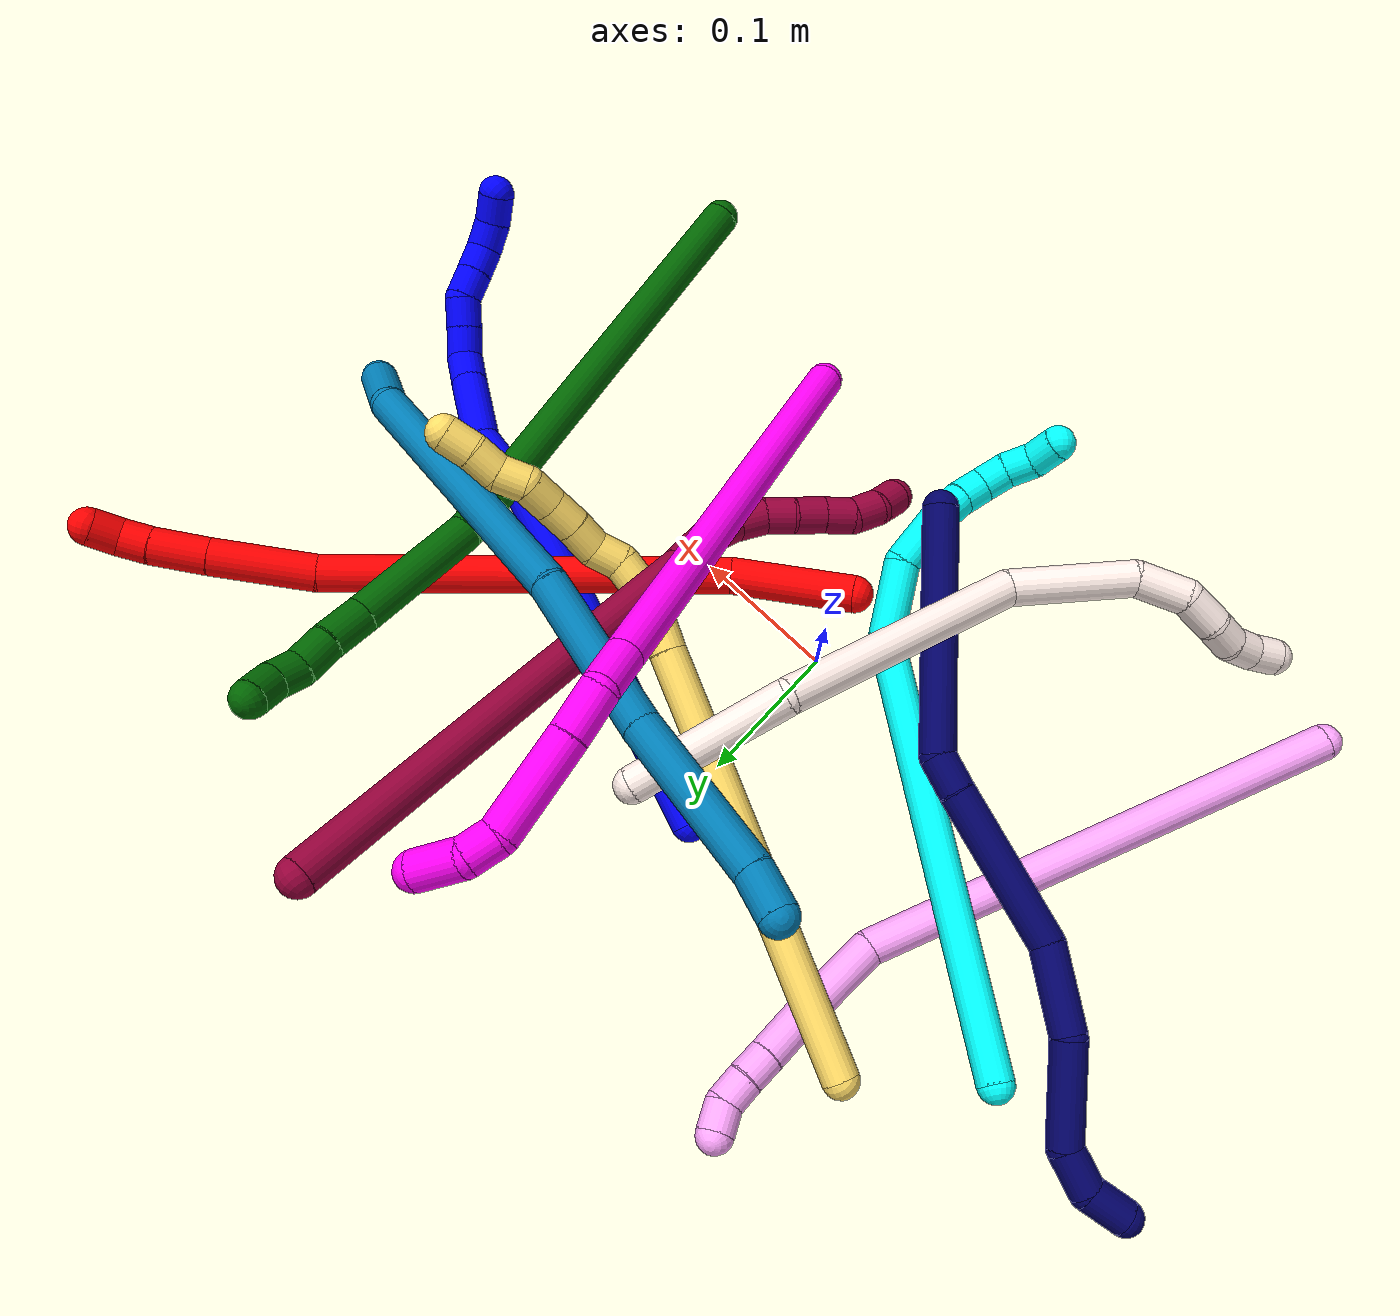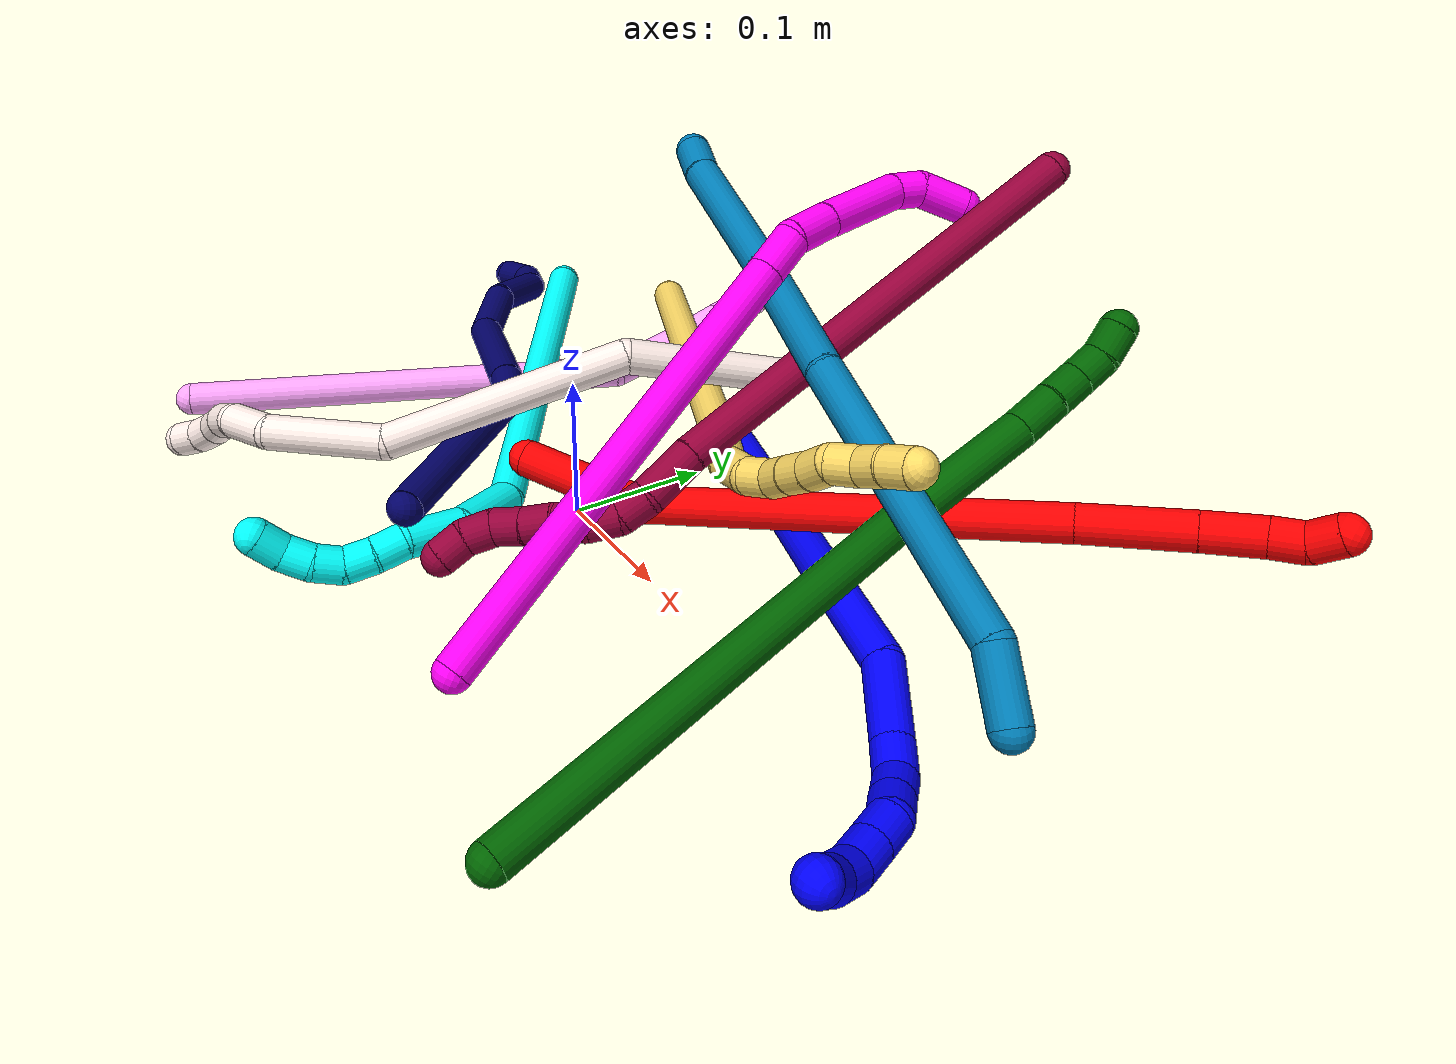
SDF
<sdf version="1.7">
 <world name="default">
  <plugin name="TubeGeneratorPlugin" filename="libtube_generator_plugin.so"/>
  <model name="photoneo_s_sensor">
   <static>1</static>
   <pose>0 0 2 1.57079 1.57079 3.14159</pose>
   <link name="link">
    <inertial><mass>0.1</mass></inertial>
    <sensor name="sensor" type="depth">
     <update_rate>30</update_rate>
     <camera>
      <horizontal_fov>1.22</horizontal_fov>
      <image><width>1920</width><height>1200</height><format>B8G8R8</format></image>
      <clip><near>0.1</near><far>4</far></clip>
      <depth_camera><output>points</output></depth_camera>
     </camera>
     <plugin name="camera_plugin" filename="libgazebo_ros_depth_camera.so">
      <baseline>0.2</baseline>
      <alwaysOn>1</alwaysOn>
      <updateRate>0.0</updateRate>
      <cameraName>camera_ir</cameraName>
      <imageTopicName>/camera/color/image_raw</imageTopicName>
      <cameraInfoTopicName>/camera/color/camera_info</cameraInfoTopicName>
      <depthImageTopicName>/camera/depth/image_raw</depthImageTopicName>
      <depthImageCameraInfoTopicName>/camera/depth/camera_info</depthImageCameraInfoTopicName>
      <pointCloudTopicName>/camera/depth/points</pointCloudTopicName>
      <frameName>fr_optical</frameName>
      <pointCloudCutoff>0.1</pointCloudCutoff>
      <pointCloudCutoffMax>2.0</pointCloudCutoffMax>
      <distortionK1>0</distortionK1>
      <distortionK2>0</distortionK2>
      <distortionK3>0</distortionK3>
      <distortionT1>0</distortionT1>
      <distortionT2>0</distortionT2>
      <CxPrime>0</CxPrime>
      <Cx>0</Cx>
      <Cy>0</Cy>
      <focalLength>0</focalLength>
      <hackBaseline>0</hackBaseline>
     </plugin>
    </sensor>
   </link>
  </model>
  <gravity>0 0 -9.8</gravity>
  <magnetic_field>6e-06 2.3e-05 -4.2e-05</magnetic_field>
  <atmosphere type="adiabatic"/>
  <physics name="default_physics" default="0" type="ode">
   <max_step_size>0.003</max_step_size>
   <real_time_factor>1</real_time_factor>
   <real_time_update_rate>1000</real_time_update_rate>
   <max_contacts>10000</max_contacts>
   <ode>
    <solver>
     <type>quick</type>
     <iters>100</iters>
     <sor>1.3</sor>
     <use_dynamic_moi_rescaling>0</use_dynamic_moi_rescaling>
    </solver>
    <constraints>
     <contact_max_correcting_vel>0</contact_max_correcting_vel>
     <contact_surface_layer>0.001</contact_surface_layer>
     <cfm>0</cfm>
     <erp>0.2</erp>
    </constraints>
   </ode>
  </physics>
  <scene><ambient>0.4 0.4 0.4 1</ambient><background>0.7 0.7 0.7 1</background><shadows>0</shadows></scene>
  <audio><device>default</device></audio>
  <spherical_coordinates>
   <surface_model>EARTH_WGS84</surface_model>
   <latitude_deg>0</latitude_deg>
   <longitude_deg>0</longitude_deg>
   <elevation>0</elevation>
   <heading_deg>0</heading_deg>
  </spherical_coordinates>
  <model name="bin">
   <static>1</static>
   <link name="bottom">
    <collision name="collision-bottom">
     <pose>0 0 -0.01 0 -0 0</pose>
     <geometry><box><size>0.8 0.6 0.02</size></box></geometry>
     <surface>
      <friction><ode><mu>100</mu><mu2>100</mu2></ode></friction>
      <contact><collide_bitmask>65535</collide_bitmask></contact>
     </surface>
    </collision>
   </link>
   <link name="west_wall">
    <collision name="collision-west_wall">
     <pose>-0.41 0 0.1 0 -0 0</pose>
     <geometry><box><size>0.02 0.6 0.2</size></box></geometry>
     <surface>
      <friction><ode><mu>100</mu><mu2>100</mu2></ode></friction>
      <contact><collide_bitmask>65535</collide_bitmask></contact>
     </surface>
    </collision>
   </link>
   <link name="east_wall">
    <collision name="collision-east_wall">
     <pose>0.41 0 0.1 0 -0 0</pose>
     <geometry><box><size>0.02 0.6 0.2</size></box></geometry>
     <surface>
      <friction><ode><mu>100</mu><mu2>100</mu2></ode></friction>
      <contact><collide_bitmask>65535</collide_bitmask></contact>
     </surface>
    </collision>
   </link>
   <link name="south_wall">
    <collision name="collision-south_wall">
     <pose>0 -0.31 0.1 0 -0 0</pose>
     <geometry><box><size>0.8 0.02 0.2</size></box></geometry>
     <surface>
      <friction><ode><mu>100</mu><mu2>100</mu2></ode></friction>
      <contact><collide_bitmask>65535</collide_bitmask></contact>
     </surface>
    </collision>
   </link>
   <link name="north_wall">
    <collision name="collision-north_wall">
     <pose>0 0.31 0.1 0 -0 0</pose>
     <geometry><box><size>0.8 0.02 0.2</size></box></geometry>
     <surface>
      <friction><ode><mu>100</mu><mu2>100</mu2></ode></friction>
      <contact><collide_bitmask>65535</collide_bitmask></contact>
     </surface>
    </collision>
   </link>
  </model>
  <model name="1">
   <static>0</static>
   <link name="1">
    <collision name="collision-cylinder-e_1_1_4">
     <pose>0.03472 -0.024136 0.116716 0.20392 0.283469 0.029197</pose>
     <geometry><cylinder><radius>0.0125</radius><length>0.248279</length></cylinder></geometry>
     <surface>
      <friction><ode><mu>1.16</mu><mu2>1.16</mu2><slip1>0</slip1><slip2>0</slip2></ode></friction>
      <contact><ode><kp>1e+06</kp><kd>1</kd><max_vel>0</max_vel><min_depth>0.001</min_depth></ode></contact>
     </surface>
    </collision>
    <visual name="visual-cylinder-e_1_1_4">
     <pose>0.03472 -0.024136 0.116716 0.20392 0.283469 0.029197</pose>
     <geometry><cylinder><radius>0.0125</radius><length>0.248279</length></cylinder></geometry>
     <material><ambient>0 0 1 1</ambient></material>
    </visual>
    <collision name="collision-cylinder-e_2_4_5">
     <pose>0.0783 -0.044589 0.259219 -0.141864 0.327826 -0.023502</pose>
     <geometry><cylinder><radius>0.0125</radius><length>0.055029</length></cylinder></geometry>
     <surface>
      <friction><ode><mu>1.16</mu><mu2>1.16</mu2><slip1>0</slip1><slip2>0</slip2></ode></friction>
      <contact><ode><kp>1e+06</kp><kd>1</kd><max_vel>0</max_vel><min_depth>0.001</min_depth></ode></contact>
     </surface>
    </collision>
    <visual name="visual-cylinder-e_2_4_5">
     <pose>0.0783 -0.044589 0.259219 -0.141864 0.327826 -0.023502</pose>
     <geometry><cylinder><radius>0.0125</radius><length>0.055029</length></cylinder></geometry>
     <material><ambient>0 0 1 1</ambient></material>
    </visual>
    <collision name="collision-cylinder-e_3_5_6">
     <pose>0.104396 -0.040665 0.304889 -0.01211 0.714198 -0.004518</pose>
     <geometry><cylinder><radius>0.0125</radius><length>0.05263</length></cylinder></geometry>
     <surface>
      <friction><ode><mu>1.16</mu><mu2>1.16</mu2><slip1>0</slip1><slip2>0</slip2></ode></friction>
      <contact><ode><kp>1e+06</kp><kd>1</kd><max_vel>0</max_vel><min_depth>0.001</min_depth></ode></contact>
     </surface>
    </collision>
    <visual name="visual-cylinder-e_3_5_6">
     <pose>0.104396 -0.040665 0.304889 -0.01211 0.714198 -0.004518</pose>
     <geometry><cylinder><radius>0.0125</radius><length>0.05263</length></cylinder></geometry>
     <material><ambient>0 0 1 1</ambient></material>
    </visual>
    <collision name="collision-cylinder-e_4_6_7">
     <pose>0.128542 -0.041268 0.333138 0.10044 0.687869 0.036001</pose>
     <geometry><cylinder><radius>0.0125</radius><length>0.021768</length></cylinder></geometry>
     <surface>
      <friction><ode><mu>1.16</mu><mu2>1.16</mu2><slip1>0</slip1><slip2>0</slip2></ode></friction>
      <contact><ode><kp>1e+06</kp><kd>1</kd><max_vel>0</max_vel><min_depth>0.001</min_depth></ode></contact>
     </surface>
    </collision>
    <visual name="visual-cylinder-e_4_6_7">
     <pose>0.128542 -0.041268 0.333138 0.10044 0.687869 0.036001</pose>
     <geometry><cylinder><radius>0.0125</radius><length>0.021768</length></cylinder></geometry>
     <material><ambient>0 0 1 1</ambient></material>
    </visual>
    <collision name="collision-cylinder-e_5_7_8">
     <pose>0.140443 -0.047749 0.348888 0.652082 0.492936 0.169715</pose>
     <geometry><cylinder><radius>0.0125</radius><length>0.021091</length></cylinder></geometry>
     <surface>
      <friction><ode><mu>1.16</mu><mu2>1.16</mu2><slip1>0</slip1><slip2>0</slip2></ode></friction>
      <contact><ode><kp>1e+06</kp><kd>1</kd><max_vel>0</max_vel><min_depth>0.001</min_depth></ode></contact>
     </surface>
    </collision>
    <visual name="visual-cylinder-e_5_7_8">
     <pose>0.140443 -0.047749 0.348888 0.652082 0.492936 0.169715</pose>
     <geometry><cylinder><radius>0.0125</radius><length>0.021091</length></cylinder></geometry>
     <material><ambient>0 0 1 1</ambient></material>
    </visual>
    <collision name="collision-cylinder-e_6_8_9">
     <pose>0.14983 -0.059086 0.363689 0.655253 0.439378 0.151493</pose>
     <geometry><cylinder><radius>0.0125</radius><length>0.020672</length></cylinder></geometry>
     <surface>
      <friction><ode><mu>1.16</mu><mu2>1.16</mu2><slip1>0</slip1><slip2>0</slip2></ode></friction>
      <contact><ode><kp>1e+06</kp><kd>1</kd><max_vel>0</max_vel><min_depth>0.001</min_depth></ode></contact>
     </surface>
    </collision>
    <visual name="visual-cylinder-e_6_8_9">
     <pose>0.14983 -0.059086 0.363689 0.655253 0.439378 0.151493</pose>
     <geometry><cylinder><radius>0.0125</radius><length>0.020672</length></cylinder></geometry>
     <material><ambient>0 0 1 1</ambient></material>
    </visual>
    <collision name="collision-cylinder-e_7_9_10">
     <pose>0.162066 -0.070131 0.375002 0.94096 0.870004 0.464138</pose>
     <geometry><cylinder><radius>0.0125</radius><length>0.020515</length></cylinder></geometry>
     <surface>
      <friction><ode><mu>1.16</mu><mu2>1.16</mu2><slip1>0</slip1><slip2>0</slip2></ode></friction>
      <contact><ode><kp>1e+06</kp><kd>1</kd><max_vel>0</max_vel><min_depth>0.001</min_depth></ode></contact>
     </surface>
    </collision>
    <visual name="visual-cylinder-e_7_9_10">
     <pose>0.162066 -0.070131 0.375002 0.94096 0.870004 0.464138</pose>
     <geometry><cylinder><radius>0.0125</radius><length>0.020515</length></cylinder></geometry>
     <material><ambient>0 0 1 1</ambient></material>
    </visual>
    <collision name="collision-cylinder-e_8_10_11">
     <pose>0.177335 -0.080966 0.382741 0.960041 0.836819 0.455003</pose>
     <geometry><cylinder><radius>0.0125</radius><length>0.020009</length></cylinder></geometry>
     <surface>
      <friction><ode><mu>1.16</mu><mu2>1.16</mu2><slip1>0</slip1><slip2>0</slip2></ode></friction>
      <contact><ode><kp>1e+06</kp><kd>1</kd><max_vel>0</max_vel><min_depth>0.001</min_depth></ode></contact>
     </surface>
    </collision>
    <visual name="visual-cylinder-e_8_10_11">
     <pose>0.177335 -0.080966 0.382741 0.960041 0.836819 0.455003</pose>
     <geometry><cylinder><radius>0.0125</radius><length>0.020009</length></cylinder></geometry>
     <material><ambient>0 0 1 1</ambient></material>
    </visual>
    <collision name="collision-cylinder-e_9_11_12">
     <pose>0.1892 -0.094601 0.390329 1.13983 0.459516 0.29756</pose>
     <geometry><cylinder><radius>0.0125</radius><length>0.020006</length></cylinder></geometry>
     <surface>
      <friction><ode><mu>1.16</mu><mu2>1.16</mu2><slip1>0</slip1><slip2>0</slip2></ode></friction>
      <contact><ode><kp>1e+06</kp><kd>1</kd><max_vel>0</max_vel><min_depth>0.001</min_depth></ode></contact>
     </surface>
    </collision>
    <visual name="visual-cylinder-e_9_11_12">
     <pose>0.1892 -0.094601 0.390329 1.13983 0.459516 0.29756</pose>
     <geometry><cylinder><radius>0.0125</radius><length>0.020006</length></cylinder></geometry>
     <material><ambient>0 0 1 1</ambient></material>
    </visual>
    <collision name="collision-cylinder-e_10_12_2">
     <pose>0.195199 -0.11165 0.398355 1.12262 0.156899 0.098777</pose>
     <geometry><cylinder><radius>0.0125</radius><length>0.020003</length></cylinder></geometry>
     <surface>
      <friction><ode><mu>1.16</mu><mu2>1.16</mu2><slip1>0</slip1><slip2>0</slip2></ode></friction>
      <contact><ode><kp>1e+06</kp><kd>1</kd><max_vel>0</max_vel><min_depth>0.001</min_depth></ode></contact>
     </surface>
    </collision>
    <visual name="visual-cylinder-e_10_12_2">
     <pose>0.195199 -0.11165 0.398355 1.12262 0.156899 0.098777</pose>
     <geometry><cylinder><radius>0.0125</radius><length>0.020003</length></cylinder></geometry>
     <material><ambient>0 0 1 1</ambient></material>
    </visual>
    <collision name="collision-sphere-2">
     <pose>0.196762 -0.120553 0.402635 0 -0 0</pose>
     <geometry><sphere><radius>0.0125</radius></sphere></geometry>
     <surface>
      <friction><ode><mu>1.16</mu><mu2>1.16</mu2><slip1>0</slip1><slip2>0</slip2></ode></friction>
      <contact><ode><kp>1e+06</kp><kd>1</kd><max_vel>0</max_vel><min_depth>0.001</min_depth></ode></contact>
     </surface>
    </collision>
    <visual name="visual-sphere-2">
     <pose>0.196762 -0.120553 0.402635 0 -0 0</pose>
     <geometry><sphere><radius>0.0125</radius></sphere></geometry>
     <material><ambient>0 0 1 1</ambient></material>
    </visual>
    <collision name="collision-sphere-12">
     <pose>0.193636 -0.102747 0.394074 0 -0 0</pose>
     <geometry><sphere><radius>0.0125</radius></sphere></geometry>
     <surface>
      <friction><ode><mu>1.16</mu><mu2>1.16</mu2><slip1>0</slip1><slip2>0</slip2></ode></friction>
      <contact><ode><kp>1e+06</kp><kd>1</kd><max_vel>0</max_vel><min_depth>0.001</min_depth></ode></contact>
     </surface>
    </collision>
    <visual name="visual-sphere-12">
     <pose>0.193636 -0.102747 0.394074 0 -0 0</pose>
     <geometry><sphere><radius>0.0125</radius></sphere></geometry>
     <material><ambient>0 0 1 1</ambient></material>
    </visual>
    <collision name="collision-sphere-11">
     <pose>0.184763 -0.086456 0.386584 0 -0 0</pose>
     <geometry><sphere><radius>0.0125</radius></sphere></geometry>
     <surface>
      <friction><ode><mu>1.16</mu><mu2>1.16</mu2><slip1>0</slip1><slip2>0</slip2></ode></friction>
      <contact><ode><kp>1e+06</kp><kd>1</kd><max_vel>0</max_vel><min_depth>0.001</min_depth></ode></contact>
     </surface>
    </collision>
    <visual name="visual-sphere-11">
     <pose>0.184763 -0.086456 0.386584 0 -0 0</pose>
     <geometry><sphere><radius>0.0125</radius></sphere></geometry>
     <material><ambient>0 0 1 1</ambient></material>
    </visual>
    <collision name="collision-sphere-10">
     <pose>0.169906 -0.075476 0.378898 0 -0 0</pose>
     <geometry><sphere><radius>0.0125</radius></sphere></geometry>
     <surface>
      <friction><ode><mu>1.16</mu><mu2>1.16</mu2><slip1>0</slip1><slip2>0</slip2></ode></friction>
      <contact><ode><kp>1e+06</kp><kd>1</kd><max_vel>0</max_vel><min_depth>0.001</min_depth></ode></contact>
     </surface>
    </collision>
    <visual name="visual-sphere-10">
     <pose>0.169906 -0.075476 0.378898 0 -0 0</pose>
     <geometry><sphere><radius>0.0125</radius></sphere></geometry>
     <material><ambient>0 0 1 1</ambient></material>
    </visual>
    <collision name="collision-sphere-9">
     <pose>0.154226 -0.064786 0.371106 0 -0 0</pose>
     <geometry><sphere><radius>0.0125</radius></sphere></geometry>
     <surface>
      <friction><ode><mu>1.16</mu><mu2>1.16</mu2><slip1>0</slip1><slip2>0</slip2></ode></friction>
      <contact><ode><kp>1e+06</kp><kd>1</kd><max_vel>0</max_vel><min_depth>0.001</min_depth></ode></contact>
     </surface>
    </collision>
    <visual name="visual-sphere-9">
     <pose>0.154226 -0.064786 0.371106 0 -0 0</pose>
     <geometry><sphere><radius>0.0125</radius></sphere></geometry>
     <material><ambient>0 0 1 1</ambient></material>
    </visual>
    <collision name="collision-sphere-4">
     <pose>0.069441 -0.048272 0.233431 0 -0 0</pose>
     <geometry><sphere><radius>0.0125</radius></sphere></geometry>
     <surface>
      <friction><ode><mu>1.16</mu><mu2>1.16</mu2><slip1>0</slip1><slip2>0</slip2></ode></friction>
      <contact><ode><kp>1e+06</kp><kd>1</kd><max_vel>0</max_vel><min_depth>0.001</min_depth></ode></contact>
     </surface>
    </collision>
    <visual name="visual-sphere-4">
     <pose>0.069441 -0.048272 0.233431 0 -0 0</pose>
     <geometry><sphere><radius>0.0125</radius></sphere></geometry>
     <material><ambient>0 0 1 1</ambient></material>
    </visual>
    <collision name="collision-sphere-1">
     <geometry><sphere><radius>0.0125</radius></sphere></geometry>
     <surface>
      <friction><ode><mu>1.16</mu><mu2>1.16</mu2><slip1>0</slip1><slip2>0</slip2></ode></friction>
      <contact><ode><kp>1e+06</kp><kd>1</kd><max_vel>0</max_vel><min_depth>0.001</min_depth></ode></contact>
     </surface>
    </collision>
    <visual name="visual-sphere-1">
     <geometry><sphere><radius>0.0125</radius></sphere></geometry>
     <material><ambient>0 0 1 1</ambient></material>
    </visual>
    <collision name="collision-sphere-8">
     <pose>0.145433 -0.053386 0.356272 0 -0 0</pose>
     <geometry><sphere><radius>0.0125</radius></sphere></geometry>
     <surface>
      <friction><ode><mu>1.16</mu><mu2>1.16</mu2><slip1>0</slip1><slip2>0</slip2></ode></friction>
      <contact><ode><kp>1e+06</kp><kd>1</kd><max_vel>0</max_vel><min_depth>0.001</min_depth></ode></contact>
     </surface>
    </collision>
    <visual name="visual-sphere-8">
     <pose>0.145433 -0.053386 0.356272 0 -0 0</pose>
     <geometry><sphere><radius>0.0125</radius></sphere></geometry>
     <material><ambient>0 0 1 1</ambient></material>
    </visual>
    <collision name="collision-sphere-5">
     <pose>0.087159 -0.040906 0.285006 0 -0 0</pose>
     <geometry><sphere><radius>0.0125</radius></sphere></geometry>
     <surface>
      <friction><ode><mu>1.16</mu><mu2>1.16</mu2><slip1>0</slip1><slip2>0</slip2></ode></friction>
      <contact><ode><kp>1e+06</kp><kd>1</kd><max_vel>0</max_vel><min_depth>0.001</min_depth></ode></contact>
     </surface>
    </collision>
    <visual name="visual-sphere-5">
     <pose>0.087159 -0.040906 0.285006 0 -0 0</pose>
     <geometry><sphere><radius>0.0125</radius></sphere></geometry>
     <material><ambient>0 0 1 1</ambient></material>
    </visual>
    <collision name="collision-sphere-6">
     <pose>0.121632 -0.040425 0.324772 0 -0 0</pose>
     <geometry><sphere><radius>0.0125</radius></sphere></geometry>
     <surface>
      <friction><ode><mu>1.16</mu><mu2>1.16</mu2><slip1>0</slip1><slip2>0</slip2></ode></friction>
      <contact><ode><kp>1e+06</kp><kd>1</kd><max_vel>0</max_vel><min_depth>0.001</min_depth></ode></contact>
     </surface>
    </collision>
    <visual name="visual-sphere-6">
     <pose>0.121632 -0.040425 0.324772 0 -0 0</pose>
     <geometry><sphere><radius>0.0125</radius></sphere></geometry>
     <material><ambient>0 0 1 1</ambient></material>
    </visual>
    <collision name="collision-sphere-7">
     <pose>0.135452 -0.042111 0.341504 0 -0 0</pose>
     <geometry><sphere><radius>0.0125</radius></sphere></geometry>
     <surface>
      <friction><ode><mu>1.16</mu><mu2>1.16</mu2><slip1>0</slip1><slip2>0</slip2></ode></friction>
      <contact><ode><kp>1e+06</kp><kd>1</kd><max_vel>0</max_vel><min_depth>0.001</min_depth></ode></contact>
     </surface>
    </collision>
    <visual name="visual-sphere-7">
     <pose>0.135452 -0.042111 0.341504 0 -0 0</pose>
     <geometry><sphere><radius>0.0125</radius></sphere></geometry>
     <material><ambient>0 0 1 1</ambient></material>
    </visual>
    <inertial>
     <pose>0.083687 -0.041796 0.22509 0 -0 0</pose>
     <mass>0.5</mass>
     <inertia>
      <ixx>0.001321</ixx>
      <ixy>0</ixy>
      <ixz>0</ixz>
      <iyy>0.001326</iyy>
      <iyz>0</iyz>
      <izz>-9.5e-05</izz>
     </inertia>
    </inertial>
   </link>
   <pose>-0.013252 0.142539 0.011487 -1.39127 0.647396 -1.46319</pose>
  </model>
  <model name="2">
   <static>0</static>
   <link name="2">
    <collision name="collision-cylinder-e_1_1_4">
     <pose>0.006972 0.002266 0.041211 -0.054936 0.167333 -0.004608</pose>
     <geometry><cylinder><radius>0.0125</radius><length>0.083716</length></cylinder></geometry>
     <surface>
      <friction><ode><mu>1.16</mu><mu2>1.16</mu2><slip1>0</slip1><slip2>0</slip2></ode></friction>
      <contact><ode><kp>1e+06</kp><kd>1</kd><max_vel>0</max_vel><min_depth>0.001</min_depth></ode></contact>
     </surface>
    </collision>
    <visual name="visual-cylinder-e_1_1_4">
     <pose>0.006972 0.002266 0.041211 -0.054936 0.167333 -0.004608</pose>
     <geometry><cylinder><radius>0.0125</radius><length>0.083716</length></cylinder></geometry>
     <material><ambient>1 0 0 1</ambient></material>
    </visual>
    <collision name="collision-cylinder-e_2_4_5">
     <pose>0.049408 0.053351 0.203459 -0.383377 0.265331 -0.051786</pose>
     <geometry><cylinder><radius>0.0125</radius><length>0.270488</length></cylinder></geometry>
     <surface>
      <friction><ode><mu>1.16</mu><mu2>1.16</mu2><slip1>0</slip1><slip2>0</slip2></ode></friction>
      <contact><ode><kp>1e+06</kp><kd>1</kd><max_vel>0</max_vel><min_depth>0.001</min_depth></ode></contact>
     </surface>
    </collision>
    <visual name="visual-cylinder-e_2_4_5">
     <pose>0.049408 0.053351 0.203459 -0.383377 0.265331 -0.051786</pose>
     <geometry><cylinder><radius>0.0125</radius><length>0.270488</length></cylinder></geometry>
     <material><ambient>1 0 0 1</ambient></material>
    </visual>
    <collision name="collision-cylinder-e_3_5_6">
     <pose>0.088785 0.114786 0.356349 -0.377126 0.113687 -0.021717</pose>
     <geometry><cylinder><radius>0.0125</radius><length>0.068966</length></cylinder></geometry>
     <surface>
      <friction><ode><mu>1.16</mu><mu2>1.16</mu2><slip1>0</slip1><slip2>0</slip2></ode></friction>
      <contact><ode><kp>1e+06</kp><kd>1</kd><max_vel>0</max_vel><min_depth>0.001</min_depth></ode></contact>
     </surface>
    </collision>
    <visual name="visual-cylinder-e_3_5_6">
     <pose>0.088785 0.114786 0.356349 -0.377126 0.113687 -0.021717</pose>
     <geometry><cylinder><radius>0.0125</radius><length>0.068966</length></cylinder></geometry>
     <material><ambient>1 0 0 1</ambient></material>
    </visual>
    <collision name="collision-cylinder-e_4_6_7">
     <pose>0.094237 0.133826 0.405261 -0.360125 0.084287 -0.015352</pose>
     <geometry><cylinder><radius>0.0125</radius><length>0.036587</length></cylinder></geometry>
     <surface>
      <friction><ode><mu>1.16</mu><mu2>1.16</mu2><slip1>0</slip1><slip2>0</slip2></ode></friction>
      <contact><ode><kp>1e+06</kp><kd>1</kd><max_vel>0</max_vel><min_depth>0.001</min_depth></ode></contact>
     </surface>
    </collision>
    <visual name="visual-cylinder-e_4_6_7">
     <pose>0.094237 0.133826 0.405261 -0.360125 0.084287 -0.015352</pose>
     <geometry><cylinder><radius>0.0125</radius><length>0.036587</length></cylinder></geometry>
     <material><ambient>1 0 0 1</ambient></material>
    </visual>
    <collision name="collision-cylinder-e_5_7_8">
     <pose>0.095849 0.143191 0.431942 -0.296731 0.007145 -0.001068</pose>
     <geometry><cylinder><radius>0.0125</radius><length>0.020124</length></cylinder></geometry>
     <surface>
      <friction><ode><mu>1.16</mu><mu2>1.16</mu2><slip1>0</slip1><slip2>0</slip2></ode></friction>
      <contact><ode><kp>1e+06</kp><kd>1</kd><max_vel>0</max_vel><min_depth>0.001</min_depth></ode></contact>
     </surface>
    </collision>
    <visual name="visual-cylinder-e_5_7_8">
     <pose>0.095849 0.143191 0.431942 -0.296731 0.007145 -0.001068</pose>
     <geometry><cylinder><radius>0.0125</radius><length>0.020124</length></cylinder></geometry>
     <material><ambient>1 0 0 1</ambient></material>
    </visual>
    <collision name="collision-cylinder-e_6_8_2">
     <pose>0.094446 0.152705 0.449036 -0.72139 -0.147105 0.055574</pose>
     <geometry><cylinder><radius>0.0125</radius><length>0.020119</length></cylinder></geometry>
     <surface>
      <friction><ode><mu>1.16</mu><mu2>1.16</mu2><slip1>0</slip1><slip2>0</slip2></ode></friction>
      <contact><ode><kp>1e+06</kp><kd>1</kd><max_vel>0</max_vel><min_depth>0.001</min_depth></ode></contact>
     </surface>
    </collision>
    <visual name="visual-cylinder-e_6_8_2">
     <pose>0.094446 0.152705 0.449036 -0.72139 -0.147105 0.055574</pose>
     <geometry><cylinder><radius>0.0125</radius><length>0.020119</length></cylinder></geometry>
     <material><ambient>1 0 0 1</ambient></material>
    </visual>
    <collision name="collision-sphere-2">
     <pose>0.092972 0.159277 0.456508 0 -0 0</pose>
     <geometry><sphere><radius>0.0125</radius></sphere></geometry>
     <surface>
      <friction><ode><mu>1.16</mu><mu2>1.16</mu2><slip1>0</slip1><slip2>0</slip2></ode></friction>
      <contact><ode><kp>1e+06</kp><kd>1</kd><max_vel>0</max_vel><min_depth>0.001</min_depth></ode></contact>
     </surface>
    </collision>
    <visual name="visual-sphere-2">
     <pose>0.092972 0.159277 0.456508 0 -0 0</pose>
     <geometry><sphere><radius>0.0125</radius></sphere></geometry>
     <material><ambient>1 0 0 1</ambient></material>
    </visual>
    <collision name="collision-sphere-4">
     <pose>0.013943 0.004533 0.082422 0 -0 0</pose>
     <geometry><sphere><radius>0.0125</radius></sphere></geometry>
     <surface>
      <friction><ode><mu>1.16</mu><mu2>1.16</mu2><slip1>0</slip1><slip2>0</slip2></ode></friction>
      <contact><ode><kp>1e+06</kp><kd>1</kd><max_vel>0</max_vel><min_depth>0.001</min_depth></ode></contact>
     </surface>
    </collision>
    <visual name="visual-sphere-4">
     <pose>0.013943 0.004533 0.082422 0 -0 0</pose>
     <geometry><sphere><radius>0.0125</radius></sphere></geometry>
     <material><ambient>1 0 0 1</ambient></material>
    </visual>
    <collision name="collision-sphere-1">
     <geometry><sphere><radius>0.0125</radius></sphere></geometry>
     <surface>
      <friction><ode><mu>1.16</mu><mu2>1.16</mu2><slip1>0</slip1><slip2>0</slip2></ode></friction>
      <contact><ode><kp>1e+06</kp><kd>1</kd><max_vel>0</max_vel><min_depth>0.001</min_depth></ode></contact>
     </surface>
    </collision>
    <visual name="visual-sphere-1">
     <geometry><sphere><radius>0.0125</radius></sphere></geometry>
     <material><ambient>1 0 0 1</ambient></material>
    </visual>
    <collision name="collision-sphere-8">
     <pose>0.095921 0.146133 0.441564 0 -0 0</pose>
     <geometry><sphere><radius>0.0125</radius></sphere></geometry>
     <surface>
      <friction><ode><mu>1.16</mu><mu2>1.16</mu2><slip1>0</slip1><slip2>0</slip2></ode></friction>
      <contact><ode><kp>1e+06</kp><kd>1</kd><max_vel>0</max_vel><min_depth>0.001</min_depth></ode></contact>
     </surface>
    </collision>
    <visual name="visual-sphere-8">
     <pose>0.095921 0.146133 0.441564 0 -0 0</pose>
     <geometry><sphere><radius>0.0125</radius></sphere></geometry>
     <material><ambient>1 0 0 1</ambient></material>
    </visual>
    <collision name="collision-sphere-5">
     <pose>0.084873 0.102169 0.324496 0 -0 0</pose>
     <geometry><sphere><radius>0.0125</radius></sphere></geometry>
     <surface>
      <friction><ode><mu>1.16</mu><mu2>1.16</mu2><slip1>0</slip1><slip2>0</slip2></ode></friction>
      <contact><ode><kp>1e+06</kp><kd>1</kd><max_vel>0</max_vel><min_depth>0.001</min_depth></ode></contact>
     </surface>
    </collision>
    <visual name="visual-sphere-5">
     <pose>0.084873 0.102169 0.324496 0 -0 0</pose>
     <geometry><sphere><radius>0.0125</radius></sphere></geometry>
     <material><ambient>1 0 0 1</ambient></material>
    </visual>
    <collision name="collision-sphere-6">
     <pose>0.092697 0.127402 0.388201 0 -0 0</pose>
     <geometry><sphere><radius>0.0125</radius></sphere></geometry>
     <surface>
      <friction><ode><mu>1.16</mu><mu2>1.16</mu2><slip1>0</slip1><slip2>0</slip2></ode></friction>
      <contact><ode><kp>1e+06</kp><kd>1</kd><max_vel>0</max_vel><min_depth>0.001</min_depth></ode></contact>
     </surface>
    </collision>
    <visual name="visual-sphere-6">
     <pose>0.092697 0.127402 0.388201 0 -0 0</pose>
     <geometry><sphere><radius>0.0125</radius></sphere></geometry>
     <material><ambient>1 0 0 1</ambient></material>
    </visual>
    <collision name="collision-sphere-7">
     <pose>0.095777 0.140249 0.42232 0 -0 0</pose>
     <geometry><sphere><radius>0.0125</radius></sphere></geometry>
     <surface>
      <friction><ode><mu>1.16</mu><mu2>1.16</mu2><slip1>0</slip1><slip2>0</slip2></ode></friction>
      <contact><ode><kp>1e+06</kp><kd>1</kd><max_vel>0</max_vel><min_depth>0.001</min_depth></ode></contact>
     </surface>
    </collision>
    <visual name="visual-sphere-7">
     <pose>0.095777 0.140249 0.42232 0 -0 0</pose>
     <geometry><sphere><radius>0.0125</radius></sphere></geometry>
     <material><ambient>1 0 0 1</ambient></material>
    </visual>
    <inertial>
     <pose>0.054696 0.066774 0.231226 0 -0 0</pose>
     <mass>0.5</mass>
     <inertia>
      <ixx>0.001613</ixx>
      <ixy>0</ixy>
      <ixz>0</ixz>
      <iyy>0.001562</iyy>
      <iyz>0</iyz>
      <izz>-0.001028</izz>
     </inertia>
    </inertial>
   </link>
   <pose>0.006617 -0.039318 0.05814 1.72063 0.398673 2.00578</pose>
  </model>
  <model name="3">
   <static>0</static>
   <link name="3">
    <collision name="collision-cylinder-e_1_1_4">
     <pose>0.011739 0.01119 -0.150633 -3.06744 0.077564 -1.61584</pose>
     <geometry><cylinder><radius>0.0125</radius><length>0.303007</length></cylinder></geometry>
     <surface>
      <friction><ode><mu>1.16</mu><mu2>1.16</mu2><slip1>0</slip1><slip2>0</slip2></ode></friction>
      <contact><ode><kp>1e+06</kp><kd>1</kd><max_vel>0</max_vel><min_depth>0.001</min_depth></ode></contact>
     </surface>
    </collision>
    <visual name="visual-cylinder-e_1_1_4">
     <pose>0.011739 0.01119 -0.150633 -3.06744 0.077564 -1.61584</pose>
     <geometry><cylinder><radius>0.0125</radius><length>0.303007</length></cylinder></geometry>
     <material><ambient>0.003922 1 0.996078 1</ambient></material>
    </visual>
    <collision name="collision-cylinder-e_2_4_5">
     <pose>0.033082 0.014104 -0.324903 2.80481 0.366167 1.65609</pose>
     <geometry><cylinder><radius>0.0125</radius><length>0.053644</length></cylinder></geometry>
     <surface>
      <friction><ode><mu>1.16</mu><mu2>1.16</mu2><slip1>0</slip1><slip2>0</slip2></ode></friction>
      <contact><ode><kp>1e+06</kp><kd>1</kd><max_vel>0</max_vel><min_depth>0.001</min_depth></ode></contact>
     </surface>
    </collision>
    <visual name="visual-cylinder-e_2_4_5">
     <pose>0.033082 0.014104 -0.324903 2.80481 0.366167 1.65609</pose>
     <geometry><cylinder><radius>0.0125</radius><length>0.053644</length></cylinder></geometry>
     <material><ambient>0.003922 1 0.996078 1</ambient></material>
    </visual>
    <collision name="collision-cylinder-e_3_5_6">
     <pose>0.048427 -0.008697 -0.362071 2.32078 0.281568 0.629753</pose>
     <geometry><cylinder><radius>0.0125</radius><length>0.041329</length></cylinder></geometry>
     <surface>
      <friction><ode><mu>1.16</mu><mu2>1.16</mu2><slip1>0</slip1><slip2>0</slip2></ode></friction>
      <contact><ode><kp>1e+06</kp><kd>1</kd><max_vel>0</max_vel><min_depth>0.001</min_depth></ode></contact>
     </surface>
    </collision>
    <visual name="visual-cylinder-e_3_5_6">
     <pose>0.048427 -0.008697 -0.362071 2.32078 0.281568 0.629753</pose>
     <geometry><cylinder><radius>0.0125</radius><length>0.041329</length></cylinder></geometry>
     <material><ambient>0.003922 1 0.996078 1</ambient></material>
    </visual>
    <collision name="collision-cylinder-e_4_6_7">
     <pose>0.053766 -0.031496 -0.381951 2.22533 -0.038683 -0.078415</pose>
     <geometry><cylinder><radius>0.0125</radius><length>0.020875</length></cylinder></geometry>
     <surface>
      <friction><ode><mu>1.16</mu><mu2>1.16</mu2><slip1>0</slip1><slip2>0</slip2></ode></friction>
      <contact><ode><kp>1e+06</kp><kd>1</kd><max_vel>0</max_vel><min_depth>0.001</min_depth></ode></contact>
     </surface>
    </collision>
    <visual name="visual-cylinder-e_4_6_7">
     <pose>0.053766 -0.031496 -0.381951 2.22533 -0.038683 -0.078415</pose>
     <geometry><cylinder><radius>0.0125</radius><length>0.020875</length></cylinder></geometry>
     <material><ambient>0.003922 1 0.996078 1</ambient></material>
    </visual>
    <collision name="collision-cylinder-e_5_7_8">
     <pose>0.053074 -0.048707 -0.39322 2.07396 -0.028212 -0.047726</pose>
     <geometry><cylinder><radius>0.0125</radius><length>0.02041</length></cylinder></geometry>
     <surface>
      <friction><ode><mu>1.16</mu><mu2>1.16</mu2><slip1>0</slip1><slip2>0</slip2></ode></friction>
      <contact><ode><kp>1e+06</kp><kd>1</kd><max_vel>0</max_vel><min_depth>0.001</min_depth></ode></contact>
     </surface>
    </collision>
    <visual name="visual-cylinder-e_5_7_8">
     <pose>0.053074 -0.048707 -0.39322 2.07396 -0.028212 -0.047726</pose>
     <geometry><cylinder><radius>0.0125</radius><length>0.02041</length></cylinder></geometry>
     <material><ambient>0.003922 1 0.996078 1</ambient></material>
    </visual>
    <collision name="collision-cylinder-e_6_8_9">
     <pose>0.056823 -0.066386 -0.40104 1.89123 0.413033 0.565011</pose>
     <geometry><cylinder><radius>0.0125</radius><length>0.020115</length></cylinder></geometry>
     <surface>
      <friction><ode><mu>1.16</mu><mu2>1.16</mu2><slip1>0</slip1><slip2>0</slip2></ode></friction>
      <contact><ode><kp>1e+06</kp><kd>1</kd><max_vel>0</max_vel><min_depth>0.001</min_depth></ode></contact>
     </surface>
    </collision>
    <visual name="visual-cylinder-e_6_8_9">
     <pose>0.056823 -0.066386 -0.40104 1.89123 0.413033 0.565011</pose>
     <geometry><cylinder><radius>0.0125</radius><length>0.020115</length></cylinder></geometry>
     <material><ambient>0.003922 1 0.996078 1</ambient></material>
    </visual>
    <collision name="collision-cylinder-e_7_9_10">
     <pose>0.065545 -0.083964 -0.404245 1.60509 0.487304 0.503608</pose>
     <geometry><cylinder><radius>0.0125</radius><length>0.020009</length></cylinder></geometry>
     <surface>
      <friction><ode><mu>1.16</mu><mu2>1.16</mu2><slip1>0</slip1><slip2>0</slip2></ode></friction>
      <contact><ode><kp>1e+06</kp><kd>1</kd><max_vel>0</max_vel><min_depth>0.001</min_depth></ode></contact>
     </surface>
    </collision>
    <visual name="visual-cylinder-e_7_9_10">
     <pose>0.065545 -0.083964 -0.404245 1.60509 0.487304 0.503608</pose>
     <geometry><cylinder><radius>0.0125</radius><length>0.020009</length></cylinder></geometry>
     <material><ambient>0.003922 1 0.996078 1</ambient></material>
    </visual>
    <collision name="collision-cylinder-e_8_10_2">
     <pose>0.07806 -0.099422 -0.405552 1.7212 0.863106 0.98336</pose>
     <geometry><cylinder><radius>0.0125</radius><length>0.02061</length></cylinder></geometry>
     <surface>
      <friction><ode><mu>1.16</mu><mu2>1.16</mu2><slip1>0</slip1><slip2>0</slip2></ode></friction>
      <contact><ode><kp>1e+06</kp><kd>1</kd><max_vel>0</max_vel><min_depth>0.001</min_depth></ode></contact>
     </surface>
    </collision>
    <visual name="visual-cylinder-e_8_10_2">
     <pose>0.07806 -0.099422 -0.405552 1.7212 0.863106 0.98336</pose>
     <geometry><cylinder><radius>0.0125</radius><length>0.02061</length></cylinder></geometry>
     <material><ambient>0.003922 1 0.996078 1</ambient></material>
    </visual>
    <collision name="collision-sphere-2">
     <pose>0.085891 -0.106046 -0.406555 0 -0 0</pose>
     <geometry><sphere><radius>0.0125</radius></sphere></geometry>
     <surface>
      <friction><ode><mu>1.16</mu><mu2>1.16</mu2><slip1>0</slip1><slip2>0</slip2></ode></friction>
      <contact><ode><kp>1e+06</kp><kd>1</kd><max_vel>0</max_vel><min_depth>0.001</min_depth></ode></contact>
     </surface>
    </collision>
    <visual name="visual-sphere-2">
     <pose>0.085891 -0.106046 -0.406555 0 -0 0</pose>
     <geometry><sphere><radius>0.0125</radius></sphere></geometry>
     <material><ambient>0.003922 1 0.996078 1</ambient></material>
    </visual>
    <collision name="collision-sphere-10">
     <pose>0.07023 -0.092799 -0.404548 0 -0 0</pose>
     <geometry><sphere><radius>0.0125</radius></sphere></geometry>
     <surface>
      <friction><ode><mu>1.16</mu><mu2>1.16</mu2><slip1>0</slip1><slip2>0</slip2></ode></friction>
      <contact><ode><kp>1e+06</kp><kd>1</kd><max_vel>0</max_vel><min_depth>0.001</min_depth></ode></contact>
     </surface>
    </collision>
    <visual name="visual-sphere-10">
     <pose>0.07023 -0.092799 -0.404548 0 -0 0</pose>
     <geometry><sphere><radius>0.0125</radius></sphere></geometry>
     <material><ambient>0.003922 1 0.996078 1</ambient></material>
    </visual>
    <collision name="collision-sphere-9">
     <pose>0.06086 -0.075129 -0.403942 0 -0 0</pose>
     <geometry><sphere><radius>0.0125</radius></sphere></geometry>
     <surface>
      <friction><ode><mu>1.16</mu><mu2>1.16</mu2><slip1>0</slip1><slip2>0</slip2></ode></friction>
      <contact><ode><kp>1e+06</kp><kd>1</kd><max_vel>0</max_vel><min_depth>0.001</min_depth></ode></contact>
     </surface>
    </collision>
    <visual name="visual-sphere-9">
     <pose>0.06086 -0.075129 -0.403942 0 -0 0</pose>
     <geometry><sphere><radius>0.0125</radius></sphere></geometry>
     <material><ambient>0.003922 1 0.996078 1</ambient></material>
    </visual>
    <collision name="collision-sphere-4">
     <pose>0.023479 0.02238 -0.301266 0 -0 0</pose>
     <geometry><sphere><radius>0.0125</radius></sphere></geometry>
     <surface>
      <friction><ode><mu>1.16</mu><mu2>1.16</mu2><slip1>0</slip1><slip2>0</slip2></ode></friction>
      <contact><ode><kp>1e+06</kp><kd>1</kd><max_vel>0</max_vel><min_depth>0.001</min_depth></ode></contact>
     </surface>
    </collision>
    <visual name="visual-sphere-4">
     <pose>0.023479 0.02238 -0.301266 0 -0 0</pose>
     <geometry><sphere><radius>0.0125</radius></sphere></geometry>
     <material><ambient>0.003922 1 0.996078 1</ambient></material>
    </visual>
    <collision name="collision-sphere-1">
     <geometry><sphere><radius>0.0125</radius></sphere></geometry>
     <surface>
      <friction><ode><mu>1.16</mu><mu2>1.16</mu2><slip1>0</slip1><slip2>0</slip2></ode></friction>
      <contact><ode><kp>1e+06</kp><kd>1</kd><max_vel>0</max_vel><min_depth>0.001</min_depth></ode></contact>
     </surface>
    </collision>
    <visual name="visual-sphere-1">
     <geometry><sphere><radius>0.0125</radius></sphere></geometry>
     <material><ambient>0.003922 1 0.996078 1</ambient></material>
    </visual>
    <collision name="collision-sphere-8">
     <pose>0.052786 -0.057643 -0.398139 0 -0 0</pose>
     <geometry><sphere><radius>0.0125</radius></sphere></geometry>
     <surface>
      <friction><ode><mu>1.16</mu><mu2>1.16</mu2><slip1>0</slip1><slip2>0</slip2></ode></friction>
      <contact><ode><kp>1e+06</kp><kd>1</kd><max_vel>0</max_vel><min_depth>0.001</min_depth></ode></contact>
     </surface>
    </collision>
    <visual name="visual-sphere-8">
     <pose>0.052786 -0.057643 -0.398139 0 -0 0</pose>
     <geometry><sphere><radius>0.0125</radius></sphere></geometry>
     <material><ambient>0.003922 1 0.996078 1</ambient></material>
    </visual>
    <collision name="collision-sphere-5">
     <pose>0.042686 0.005828 -0.34854 0 -0 0</pose>
     <geometry><sphere><radius>0.0125</radius></sphere></geometry>
     <surface>
      <friction><ode><mu>1.16</mu><mu2>1.16</mu2><slip1>0</slip1><slip2>0</slip2></ode></friction>
      <contact><ode><kp>1e+06</kp><kd>1</kd><max_vel>0</max_vel><min_depth>0.001</min_depth></ode></contact>
     </surface>
    </collision>
    <visual name="visual-sphere-5">
     <pose>0.042686 0.005828 -0.34854 0 -0 0</pose>
     <geometry><sphere><radius>0.0125</radius></sphere></geometry>
     <material><ambient>0.003922 1 0.996078 1</ambient></material>
    </visual>
    <collision name="collision-sphere-6">
     <pose>0.054169 -0.023222 -0.375602 0 -0 0</pose>
     <geometry><sphere><radius>0.0125</radius></sphere></geometry>
     <surface>
      <friction><ode><mu>1.16</mu><mu2>1.16</mu2><slip1>0</slip1><slip2>0</slip2></ode></friction>
      <contact><ode><kp>1e+06</kp><kd>1</kd><max_vel>0</max_vel><min_depth>0.001</min_depth></ode></contact>
     </surface>
    </collision>
    <visual name="visual-sphere-6">
     <pose>0.054169 -0.023222 -0.375602 0 -0 0</pose>
     <geometry><sphere><radius>0.0125</radius></sphere></geometry>
     <material><ambient>0.003922 1 0.996078 1</ambient></material>
    </visual>
    <collision name="collision-sphere-7">
     <pose>0.053362 -0.03977 -0.388301 0 -0 0</pose>
     <geometry><sphere><radius>0.0125</radius></sphere></geometry>
     <surface>
      <friction><ode><mu>1.16</mu><mu2>1.16</mu2><slip1>0</slip1><slip2>0</slip2></ode></friction>
      <contact><ode><kp>1e+06</kp><kd>1</kd><max_vel>0</max_vel><min_depth>0.001</min_depth></ode></contact>
     </surface>
    </collision>
    <visual name="visual-sphere-7">
     <pose>0.053362 -0.03977 -0.388301 0 -0 0</pose>
     <geometry><sphere><radius>0.0125</radius></sphere></geometry>
     <material><ambient>0.003922 1 0.996078 1</ambient></material>
    </visual>
    <inertial>
     <pose>0.027204 -0.005857 -0.237098 0 -0 0</pose>
     <mass>0.5</mass>
     <inertia>
      <ixx>-0.002388</ixx>
      <ixy>0</ixy>
      <ixz>0</ixz>
      <iyy>-0.002192</iyy>
      <iyz>0</iyz>
      <izz>-0.000378</izz>
     </inertia>
    </inertial>
   </link>
   <pose>-0.268435 0.133783 0.049957 0.325672 -1.34844 -1.02838</pose>
  </model>
  <model name="4">
   <static>0</static>
   <link name="4">
    <collision name="collision-cylinder-e_1_1_4">
     <pose>0.045262 0.116419 -0.060204 -2.04806 0.33252 -0.538033</pose>
     <geometry><cylinder><radius>0.0125</radius><length>0.27732</length></cylinder></geometry>
     <surface>
      <friction><ode><mu>1.16</mu><mu2>1.16</mu2><slip1>0</slip1><slip2>0</slip2></ode></friction>
      <contact><ode><kp>1e+06</kp><kd>1</kd><max_vel>0</max_vel><min_depth>0.001</min_depth></ode></contact>
     </surface>
    </collision>
    <visual name="visual-cylinder-e_1_1_4">
     <pose>0.045262 0.116419 -0.060204 -2.04806 0.33252 -0.538033</pose>
     <geometry><cylinder><radius>0.0125</radius><length>0.27732</length></cylinder></geometry>
     <material><ambient>1 0.65098 0.996078 1</ambient></material>
    </visual>
    <collision name="collision-cylinder-e_2_4_5">
     <pose>0.100718 0.25888 -0.133915 -2.04923 0.334422 -0.5417</pose>
     <geometry><cylinder><radius>0.0125</radius><length>0.062113</length></cylinder></geometry>
     <surface>
      <friction><ode><mu>1.16</mu><mu2>1.16</mu2><slip1>0</slip1><slip2>0</slip2></ode></friction>
      <contact><ode><kp>1e+06</kp><kd>1</kd><max_vel>0</max_vel><min_depth>0.001</min_depth></ode></contact>
     </surface>
    </collision>
    <visual name="visual-cylinder-e_2_4_5">
     <pose>0.100718 0.25888 -0.133915 -2.04923 0.334422 -0.5417</pose>
     <geometry><cylinder><radius>0.0125</radius><length>0.062113</length></cylinder></geometry>
     <material><ambient>1 0.65098 0.996078 1</ambient></material>
    </visual>
    <collision name="collision-cylinder-e_3_5_6">
     <pose>0.124242 0.301066 -0.168582 -2.48987 0.464323 -1.22101</pose>
     <geometry><cylinder><radius>0.0125</radius><length>0.059535</length></cylinder></geometry>
     <surface>
      <friction><ode><mu>1.16</mu><mu2>1.16</mu2><slip1>0</slip1><slip2>0</slip2></ode></friction>
      <contact><ode><kp>1e+06</kp><kd>1</kd><max_vel>0</max_vel><min_depth>0.001</min_depth></ode></contact>
     </surface>
    </collision>
    <visual name="visual-cylinder-e_3_5_6">
     <pose>0.124242 0.301066 -0.168582 -2.48987 0.464323 -1.22101</pose>
     <geometry><cylinder><radius>0.0125</radius><length>0.059535</length></cylinder></geometry>
     <material><ambient>1 0.65098 0.996078 1</ambient></material>
    </visual>
    <collision name="collision-cylinder-e_4_6_7">
     <pose>0.14668 0.32719 -0.204922 -2.55999 0.464738 -1.33808</pose>
     <geometry><cylinder><radius>0.0125</radius><length>0.040642</length></cylinder></geometry>
     <surface>
      <friction><ode><mu>1.16</mu><mu2>1.16</mu2><slip1>0</slip1><slip2>0</slip2></ode></friction>
      <contact><ode><kp>1e+06</kp><kd>1</kd><max_vel>0</max_vel><min_depth>0.001</min_depth></ode></contact>
     </surface>
    </collision>
    <visual name="visual-cylinder-e_4_6_7">
     <pose>0.14668 0.32719 -0.204922 -2.55999 0.464738 -1.33808</pose>
     <geometry><cylinder><radius>0.0125</radius><length>0.040642</length></cylinder></geometry>
     <material><ambient>1 0.65098 0.996078 1</ambient></material>
    </visual>
    <collision name="collision-cylinder-e_5_7_8">
     <pose>0.160362 0.34236 -0.227388 -2.52268 0.472621 -1.29105</pose>
     <geometry><cylinder><radius>0.0125</radius><length>0.020097</length></cylinder></geometry>
     <surface>
      <friction><ode><mu>1.16</mu><mu2>1.16</mu2><slip1>0</slip1><slip2>0</slip2></ode></friction>
      <contact><ode><kp>1e+06</kp><kd>1</kd><max_vel>0</max_vel><min_depth>0.001</min_depth></ode></contact>
     </surface>
    </collision>
    <visual name="visual-cylinder-e_5_7_8">
     <pose>0.160362 0.34236 -0.227388 -2.52268 0.472621 -1.29105</pose>
     <geometry><cylinder><radius>0.0125</radius><length>0.020097</length></cylinder></geometry>
     <material><ambient>1 0.65098 0.996078 1</ambient></material>
    </visual>
    <collision name="collision-cylinder-e_6_8_9">
     <pose>0.170363 0.352703 -0.24144 -2.49069 0.568036 -1.42633</pose>
     <geometry><cylinder><radius>0.0125</radius><length>0.020174</length></cylinder></geometry>
     <surface>
      <friction><ode><mu>1.16</mu><mu2>1.16</mu2><slip1>0</slip1><slip2>0</slip2></ode></friction>
      <contact><ode><kp>1e+06</kp><kd>1</kd><max_vel>0</max_vel><min_depth>0.001</min_depth></ode></contact>
     </surface>
    </collision>
    <visual name="visual-cylinder-e_6_8_9">
     <pose>0.170363 0.352703 -0.24144 -2.49069 0.568036 -1.42633</pose>
     <geometry><cylinder><radius>0.0125</radius><length>0.020174</length></cylinder></geometry>
     <material><ambient>1 0.65098 0.996078 1</ambient></material>
    </visual>
    <collision name="collision-cylinder-e_7_9_2">
     <pose>0.182421 0.35896 -0.255686 -2.99492 0.719888 -2.756</pose>
     <geometry><cylinder><radius>0.0125</radius><length>0.020118</length></cylinder></geometry>
     <surface>
      <friction><ode><mu>1.16</mu><mu2>1.16</mu2><slip1>0</slip1><slip2>0</slip2></ode></friction>
      <contact><ode><kp>1e+06</kp><kd>1</kd><max_vel>0</max_vel><min_depth>0.001</min_depth></ode></contact>
     </surface>
    </collision>
    <visual name="visual-cylinder-e_7_9_2">
     <pose>0.182421 0.35896 -0.255686 -2.99492 0.719888 -2.756</pose>
     <geometry><cylinder><radius>0.0125</radius><length>0.020118</length></cylinder></geometry>
     <material><ambient>1 0.65098 0.996078 1</ambient></material>
    </visual>
    <collision name="collision-sphere-2">
     <pose>0.189053 0.360066 -0.263168 0 -0 0</pose>
     <geometry><sphere><radius>0.0125</radius></sphere></geometry>
     <surface>
      <friction><ode><mu>1.16</mu><mu2>1.16</mu2><slip1>0</slip1><slip2>0</slip2></ode></friction>
      <contact><ode><kp>1e+06</kp><kd>1</kd><max_vel>0</max_vel><min_depth>0.001</min_depth></ode></contact>
     </surface>
    </collision>
    <visual name="visual-sphere-2">
     <pose>0.189053 0.360066 -0.263168 0 -0 0</pose>
     <geometry><sphere><radius>0.0125</radius></sphere></geometry>
     <material><ambient>1 0.65098 0.996078 1</ambient></material>
    </visual>
    <collision name="collision-sphere-9">
     <pose>0.175789 0.357855 -0.248204 0 -0 0</pose>
     <geometry><sphere><radius>0.0125</radius></sphere></geometry>
     <surface>
      <friction><ode><mu>1.16</mu><mu2>1.16</mu2><slip1>0</slip1><slip2>0</slip2></ode></friction>
      <contact><ode><kp>1e+06</kp><kd>1</kd><max_vel>0</max_vel><min_depth>0.001</min_depth></ode></contact>
     </surface>
    </collision>
    <visual name="visual-sphere-9">
     <pose>0.175789 0.357855 -0.248204 0 -0 0</pose>
     <geometry><sphere><radius>0.0125</radius></sphere></geometry>
     <material><ambient>1 0.65098 0.996078 1</ambient></material>
    </visual>
    <collision name="collision-sphere-4">
     <pose>0.090524 0.232838 -0.120409 0 -0 0</pose>
     <geometry><sphere><radius>0.0125</radius></sphere></geometry>
     <surface>
      <friction><ode><mu>1.16</mu><mu2>1.16</mu2><slip1>0</slip1><slip2>0</slip2></ode></friction>
      <contact><ode><kp>1e+06</kp><kd>1</kd><max_vel>0</max_vel><min_depth>0.001</min_depth></ode></contact>
     </surface>
    </collision>
    <visual name="visual-sphere-4">
     <pose>0.090524 0.232838 -0.120409 0 -0 0</pose>
     <geometry><sphere><radius>0.0125</radius></sphere></geometry>
     <material><ambient>1 0.65098 0.996078 1</ambient></material>
    </visual>
    <collision name="collision-sphere-1">
     <geometry><sphere><radius>0.0125</radius></sphere></geometry>
     <surface>
      <friction><ode><mu>1.16</mu><mu2>1.16</mu2><slip1>0</slip1><slip2>0</slip2></ode></friction>
      <contact><ode><kp>1e+06</kp><kd>1</kd><max_vel>0</max_vel><min_depth>0.001</min_depth></ode></contact>
     </surface>
    </collision>
    <visual name="visual-sphere-1">
     <geometry><sphere><radius>0.0125</radius></sphere></geometry>
     <material><ambient>1 0.65098 0.996078 1</ambient></material>
    </visual>
    <collision name="collision-sphere-8">
     <pose>0.164936 0.347551 -0.234675 0 -0 0</pose>
     <geometry><sphere><radius>0.0125</radius></sphere></geometry>
     <surface>
      <friction><ode><mu>1.16</mu><mu2>1.16</mu2><slip1>0</slip1><slip2>0</slip2></ode></friction>
      <contact><ode><kp>1e+06</kp><kd>1</kd><max_vel>0</max_vel><min_depth>0.001</min_depth></ode></contact>
     </surface>
    </collision>
    <visual name="visual-sphere-8">
     <pose>0.164936 0.347551 -0.234675 0 -0 0</pose>
     <geometry><sphere><radius>0.0125</radius></sphere></geometry>
     <material><ambient>1 0.65098 0.996078 1</ambient></material>
    </visual>
    <collision name="collision-sphere-5">
     <pose>0.110911 0.284922 -0.147421 0 -0 0</pose>
     <geometry><sphere><radius>0.0125</radius></sphere></geometry>
     <surface>
      <friction><ode><mu>1.16</mu><mu2>1.16</mu2><slip1>0</slip1><slip2>0</slip2></ode></friction>
      <contact><ode><kp>1e+06</kp><kd>1</kd><max_vel>0</max_vel><min_depth>0.001</min_depth></ode></contact>
     </surface>
    </collision>
    <visual name="visual-sphere-5">
     <pose>0.110911 0.284922 -0.147421 0 -0 0</pose>
     <geometry><sphere><radius>0.0125</radius></sphere></geometry>
     <material><ambient>1 0.65098 0.996078 1</ambient></material>
    </visual>
    <collision name="collision-sphere-6">
     <pose>0.137572 0.31721 -0.189743 0 -0 0</pose>
     <geometry><sphere><radius>0.0125</radius></sphere></geometry>
     <surface>
      <friction><ode><mu>1.16</mu><mu2>1.16</mu2><slip1>0</slip1><slip2>0</slip2></ode></friction>
      <contact><ode><kp>1e+06</kp><kd>1</kd><max_vel>0</max_vel><min_depth>0.001</min_depth></ode></contact>
     </surface>
    </collision>
    <visual name="visual-sphere-6">
     <pose>0.137572 0.31721 -0.189743 0 -0 0</pose>
     <geometry><sphere><radius>0.0125</radius></sphere></geometry>
     <material><ambient>1 0.65098 0.996078 1</ambient></material>
    </visual>
    <collision name="collision-sphere-7">
     <pose>0.155788 0.33717 -0.220101 0 -0 0</pose>
     <geometry><sphere><radius>0.0125</radius></sphere></geometry>
     <surface>
      <friction><ode><mu>1.16</mu><mu2>1.16</mu2><slip1>0</slip1><slip2>0</slip2></ode></friction>
      <contact><ode><kp>1e+06</kp><kd>1</kd><max_vel>0</max_vel><min_depth>0.001</min_depth></ode></contact>
     </surface>
    </collision>
    <visual name="visual-sphere-7">
     <pose>0.155788 0.33717 -0.220101 0 -0 0</pose>
     <geometry><sphere><radius>0.0125</radius></sphere></geometry>
     <material><ambient>1 0.65098 0.996078 1</ambient></material>
    </visual>
    <inertial>
     <pose>0.084992 0.201609 -0.115927 0 -0 0</pose>
     <mass>0.5</mass>
     <inertia>
      <ixx>0.000588</ixx>
      <ixy>0</ixy>
      <ixz>0</ixz>
      <iyy>-0.001318</iyy>
      <iyz>0</iyz>
      <izz>-0.002162</izz>
     </inertia>
    </inertial>
   </link>
   <pose>-0.289718 -0.189933 0.0115 -2.85577 0.50361 2.3537</pose>
  </model>
  <model name="5">
   <static>0</static>
   <link name="5">
    <collision name="collision-cylinder-e_1_1_4">
     <pose>0.090066 -0.036038 0.108752 0.319985 0.666233 0.111557</pose>
     <geometry><cylinder><radius>0.0125</radius><length>0.291463</length></cylinder></geometry>
     <surface>
      <friction><ode><mu>1.16</mu><mu2>1.16</mu2><slip1>0</slip1><slip2>0</slip2></ode></friction>
      <contact><ode><kp>1e+06</kp><kd>1</kd><max_vel>0</max_vel><min_depth>0.001</min_depth></ode></contact>
     </surface>
    </collision>
    <visual name="visual-cylinder-e_1_1_4">
     <pose>0.090066 -0.036038 0.108752 0.319985 0.666233 0.111557</pose>
     <geometry><cylinder><radius>0.0125</radius><length>0.291463</length></cylinder></geometry>
     <material><ambient>1 0.858824 0.4 1</ambient></material>
    </visual>
    <collision name="collision-cylinder-e_2_4_5">
     <pose>0.191962 -0.077432 0.230957 0.378981 0.68496 0.136546</pose>
     <geometry><cylinder><radius>0.0125</radius><length>0.037396</length></cylinder></geometry>
     <surface>
      <friction><ode><mu>1.16</mu><mu2>1.16</mu2><slip1>0</slip1><slip2>0</slip2></ode></friction>
      <contact><ode><kp>1e+06</kp><kd>1</kd><max_vel>0</max_vel><min_depth>0.001</min_depth></ode></contact>
     </surface>
    </collision>
    <visual name="visual-cylinder-e_2_4_5">
     <pose>0.191962 -0.077432 0.230957 0.378981 0.68496 0.136546</pose>
     <geometry><cylinder><radius>0.0125</radius><length>0.037396</length></cylinder></geometry>
     <material><ambient>1 0.858824 0.4 1</ambient></material>
    </visual>
    <collision name="collision-cylinder-e_3_5_6">
     <pose>0.210759 -0.082738 0.25765 -0.003907 0.484478 -0.000965</pose>
     <geometry><cylinder><radius>0.0125</radius><length>0.029923</length></cylinder></geometry>
     <surface>
      <friction><ode><mu>1.16</mu><mu2>1.16</mu2><slip1>0</slip1><slip2>0</slip2></ode></friction>
      <contact><ode><kp>1e+06</kp><kd>1</kd><max_vel>0</max_vel><min_depth>0.001</min_depth></ode></contact>
     </surface>
    </collision>
    <visual name="visual-cylinder-e_3_5_6">
     <pose>0.210759 -0.082738 0.25765 -0.003907 0.484478 -0.000965</pose>
     <geometry><cylinder><radius>0.0125</radius><length>0.029923</length></cylinder></geometry>
     <material><ambient>1 0.858824 0.4 1</ambient></material>
    </visual>
    <collision name="collision-cylinder-e_4_6_7">
     <pose>0.220716 -0.078377 0.279498 -0.464146 0.301046 -0.071658</pose>
     <geometry><cylinder><radius>0.0125</radius><length>0.020161</length></cylinder></geometry>
     <surface>
      <friction><ode><mu>1.16</mu><mu2>1.16</mu2><slip1>0</slip1><slip2>0</slip2></ode></friction>
      <contact><ode><kp>1e+06</kp><kd>1</kd><max_vel>0</max_vel><min_depth>0.001</min_depth></ode></contact>
     </surface>
    </collision>
    <visual name="visual-cylinder-e_4_6_7">
     <pose>0.220716 -0.078377 0.279498 -0.464146 0.301046 -0.071658</pose>
     <geometry><cylinder><radius>0.0125</radius><length>0.020161</length></cylinder></geometry>
     <material><ambient>1 0.858824 0.4 1</ambient></material>
    </visual>
    <collision name="collision-cylinder-e_5_7_8">
     <pose>0.224796 -0.07329 0.298275 -0.076287 0.106532 -0.004069</pose>
     <geometry><cylinder><radius>0.0125</radius><length>0.020512</length></cylinder></geometry>
     <surface>
      <friction><ode><mu>1.16</mu><mu2>1.16</mu2><slip1>0</slip1><slip2>0</slip2></ode></friction>
      <contact><ode><kp>1e+06</kp><kd>1</kd><max_vel>0</max_vel><min_depth>0.001</min_depth></ode></contact>
     </surface>
    </collision>
    <visual name="visual-cylinder-e_5_7_8">
     <pose>0.224796 -0.07329 0.298275 -0.076287 0.106532 -0.004069</pose>
     <geometry><cylinder><radius>0.0125</radius><length>0.020512</length></cylinder></geometry>
     <material><ambient>1 0.858824 0.4 1</ambient></material>
    </visual>
    <collision name="collision-cylinder-e_6_8_9">
     <pose>0.227071 -0.07088 0.318492 -0.161097 0.115808 -0.009359</pose>
     <geometry><cylinder><radius>0.0125</radius><length>0.020498</length></cylinder></geometry>
     <surface>
      <friction><ode><mu>1.16</mu><mu2>1.16</mu2><slip1>0</slip1><slip2>0</slip2></ode></friction>
      <contact><ode><kp>1e+06</kp><kd>1</kd><max_vel>0</max_vel><min_depth>0.001</min_depth></ode></contact>
     </surface>
    </collision>
    <visual name="visual-cylinder-e_6_8_9">
     <pose>0.227071 -0.07088 0.318492 -0.161097 0.115808 -0.009359</pose>
     <geometry><cylinder><radius>0.0125</radius><length>0.020498</length></cylinder></geometry>
     <material><ambient>1 0.858824 0.4 1</ambient></material>
    </visual>
    <collision name="collision-cylinder-e_7_9_10">
     <pose>0.228457 -0.067771 0.338436 -0.148023 0.020225 -0.0015</pose>
     <geometry><cylinder><radius>0.0125</radius><length>0.020013</length></cylinder></geometry>
     <surface>
      <friction><ode><mu>1.16</mu><mu2>1.16</mu2><slip1>0</slip1><slip2>0</slip2></ode></friction>
      <contact><ode><kp>1e+06</kp><kd>1</kd><max_vel>0</max_vel><min_depth>0.001</min_depth></ode></contact>
     </surface>
    </collision>
    <visual name="visual-cylinder-e_7_9_10">
     <pose>0.228457 -0.067771 0.338436 -0.148023 0.020225 -0.0015</pose>
     <geometry><cylinder><radius>0.0125</radius><length>0.020013</length></cylinder></geometry>
     <material><ambient>1 0.858824 0.4 1</ambient></material>
    </visual>
    <collision name="collision-cylinder-e_8_10_11">
     <pose>0.231651 -0.060987 0.356261 -0.58995 0.303798 -0.092955</pose>
     <geometry><cylinder><radius>0.0125</radius><length>0.020002</length></cylinder></geometry>
     <surface>
      <friction><ode><mu>1.16</mu><mu2>1.16</mu2><slip1>0</slip1><slip2>0</slip2></ode></friction>
      <contact><ode><kp>1e+06</kp><kd>1</kd><max_vel>0</max_vel><min_depth>0.001</min_depth></ode></contact>
     </surface>
    </collision>
    <visual name="visual-cylinder-e_8_10_11">
     <pose>0.231651 -0.060987 0.356261 -0.58995 0.303798 -0.092955</pose>
     <geometry><cylinder><radius>0.0125</radius><length>0.020002</length></cylinder></geometry>
     <material><ambient>1 0.858824 0.4 1</ambient></material>
    </visual>
    <collision name="collision-cylinder-e_9_11_12">
     <pose>0.236877 -0.053727 0.373741 -0.20153 0.22526 -0.022871</pose>
     <geometry><cylinder><radius>0.0125</radius><length>0.02</length></cylinder></geometry>
     <surface>
      <friction><ode><mu>1.16</mu><mu2>1.16</mu2><slip1>0</slip1><slip2>0</slip2></ode></friction>
      <contact><ode><kp>1e+06</kp><kd>1</kd><max_vel>0</max_vel><min_depth>0.001</min_depth></ode></contact>
     </surface>
    </collision>
    <visual name="visual-cylinder-e_9_11_12">
     <pose>0.236877 -0.053727 0.373741 -0.20153 0.22526 -0.022871</pose>
     <geometry><cylinder><radius>0.0125</radius><length>0.02</length></cylinder></geometry>
     <material><ambient>1 0.858824 0.4 1</ambient></material>
    </visual>
    <collision name="collision-cylinder-e_10_12_2">
     <pose>0.242044 -0.048409 0.392256 -0.359219 0.297302 -0.054368</pose>
     <geometry><cylinder><radius>0.0125</radius><length>0.020032</length></cylinder></geometry>
     <surface>
      <friction><ode><mu>1.16</mu><mu2>1.16</mu2><slip1>0</slip1><slip2>0</slip2></ode></friction>
      <contact><ode><kp>1e+06</kp><kd>1</kd><max_vel>0</max_vel><min_depth>0.001</min_depth></ode></contact>
     </surface>
    </collision>
    <visual name="visual-cylinder-e_10_12_2">
     <pose>0.242044 -0.048409 0.392256 -0.359219 0.297302 -0.054368</pose>
     <geometry><cylinder><radius>0.0125</radius><length>0.020032</length></cylinder></geometry>
     <material><ambient>1 0.858824 0.4 1</ambient></material>
    </visual>
    <collision name="collision-sphere-2">
     <pose>0.244978 -0.045043 0.401221 0 -0 0</pose>
     <geometry><sphere><radius>0.0125</radius></sphere></geometry>
     <surface>
      <friction><ode><mu>1.16</mu><mu2>1.16</mu2><slip1>0</slip1><slip2>0</slip2></ode></friction>
      <contact><ode><kp>1e+06</kp><kd>1</kd><max_vel>0</max_vel><min_depth>0.001</min_depth></ode></contact>
     </surface>
    </collision>
    <visual name="visual-sphere-2">
     <pose>0.244978 -0.045043 0.401221 0 -0 0</pose>
     <geometry><sphere><radius>0.0125</radius></sphere></geometry>
     <material><ambient>1 0.858824 0.4 1</ambient></material>
    </visual>
    <collision name="collision-sphere-12">
     <pose>0.23911 -0.051776 0.383291 0 -0 0</pose>
     <geometry><sphere><radius>0.0125</radius></sphere></geometry>
     <surface>
      <friction><ode><mu>1.16</mu><mu2>1.16</mu2><slip1>0</slip1><slip2>0</slip2></ode></friction>
      <contact><ode><kp>1e+06</kp><kd>1</kd><max_vel>0</max_vel><min_depth>0.001</min_depth></ode></contact>
     </surface>
    </collision>
    <visual name="visual-sphere-12">
     <pose>0.23911 -0.051776 0.383291 0 -0 0</pose>
     <geometry><sphere><radius>0.0125</radius></sphere></geometry>
     <material><ambient>1 0.858824 0.4 1</ambient></material>
    </visual>
    <collision name="collision-sphere-11">
     <pose>0.234643 -0.055678 0.364191 0 -0 0</pose>
     <geometry><sphere><radius>0.0125</radius></sphere></geometry>
     <surface>
      <friction><ode><mu>1.16</mu><mu2>1.16</mu2><slip1>0</slip1><slip2>0</slip2></ode></friction>
      <contact><ode><kp>1e+06</kp><kd>1</kd><max_vel>0</max_vel><min_depth>0.001</min_depth></ode></contact>
     </surface>
    </collision>
    <visual name="visual-sphere-11">
     <pose>0.234643 -0.055678 0.364191 0 -0 0</pose>
     <geometry><sphere><radius>0.0125</radius></sphere></geometry>
     <material><ambient>1 0.858824 0.4 1</ambient></material>
    </visual>
    <collision name="collision-sphere-10">
     <pose>0.22866 -0.066296 0.348331 0 -0 0</pose>
     <geometry><sphere><radius>0.0125</radius></sphere></geometry>
     <surface>
      <friction><ode><mu>1.16</mu><mu2>1.16</mu2><slip1>0</slip1><slip2>0</slip2></ode></friction>
      <contact><ode><kp>1e+06</kp><kd>1</kd><max_vel>0</max_vel><min_depth>0.001</min_depth></ode></contact>
     </surface>
    </collision>
    <visual name="visual-sphere-10">
     <pose>0.22866 -0.066296 0.348331 0 -0 0</pose>
     <geometry><sphere><radius>0.0125</radius></sphere></geometry>
     <material><ambient>1 0.858824 0.4 1</ambient></material>
    </visual>
    <collision name="collision-sphere-9">
     <pose>0.228255 -0.069247 0.32854 0 -0 0</pose>
     <geometry><sphere><radius>0.0125</radius></sphere></geometry>
     <surface>
      <friction><ode><mu>1.16</mu><mu2>1.16</mu2><slip1>0</slip1><slip2>0</slip2></ode></friction>
      <contact><ode><kp>1e+06</kp><kd>1</kd><max_vel>0</max_vel><min_depth>0.001</min_depth></ode></contact>
     </surface>
    </collision>
    <visual name="visual-sphere-9">
     <pose>0.228255 -0.069247 0.32854 0 -0 0</pose>
     <geometry><sphere><radius>0.0125</radius></sphere></geometry>
     <material><ambient>1 0.858824 0.4 1</ambient></material>
    </visual>
    <collision name="collision-sphere-4">
     <pose>0.180133 -0.072075 0.217504 0 -0 0</pose>
     <geometry><sphere><radius>0.0125</radius></sphere></geometry>
     <surface>
      <friction><ode><mu>1.16</mu><mu2>1.16</mu2><slip1>0</slip1><slip2>0</slip2></ode></friction>
      <contact><ode><kp>1e+06</kp><kd>1</kd><max_vel>0</max_vel><min_depth>0.001</min_depth></ode></contact>
     </surface>
    </collision>
    <visual name="visual-sphere-4">
     <pose>0.180133 -0.072075 0.217504 0 -0 0</pose>
     <geometry><sphere><radius>0.0125</radius></sphere></geometry>
     <material><ambient>1 0.858824 0.4 1</ambient></material>
    </visual>
    <collision name="collision-sphere-1">
     <geometry><sphere><radius>0.0125</radius></sphere></geometry>
     <surface>
      <friction><ode><mu>1.16</mu><mu2>1.16</mu2><slip1>0</slip1><slip2>0</slip2></ode></friction>
      <contact><ode><kp>1e+06</kp><kd>1</kd><max_vel>0</max_vel><min_depth>0.001</min_depth></ode></contact>
     </surface>
    </collision>
    <visual name="visual-sphere-1">
     <geometry><sphere><radius>0.0125</radius></sphere></geometry>
     <material><ambient>1 0.858824 0.4 1</ambient></material>
    </visual>
    <collision name="collision-sphere-8">
     <pose>0.225886 -0.072513 0.308443 0 -0 0</pose>
     <geometry><sphere><radius>0.0125</radius></sphere></geometry>
     <surface>
      <friction><ode><mu>1.16</mu><mu2>1.16</mu2><slip1>0</slip1><slip2>0</slip2></ode></friction>
      <contact><ode><kp>1e+06</kp><kd>1</kd><max_vel>0</max_vel><min_depth>0.001</min_depth></ode></contact>
     </surface>
    </collision>
    <visual name="visual-sphere-8">
     <pose>0.225886 -0.072513 0.308443 0 -0 0</pose>
     <geometry><sphere><radius>0.0125</radius></sphere></geometry>
     <material><ambient>1 0.858824 0.4 1</ambient></material>
    </visual>
    <collision name="collision-sphere-5">
     <pose>0.203791 -0.08279 0.24441 0 -0 0</pose>
     <geometry><sphere><radius>0.0125</radius></sphere></geometry>
     <surface>
      <friction><ode><mu>1.16</mu><mu2>1.16</mu2><slip1>0</slip1><slip2>0</slip2></ode></friction>
      <contact><ode><kp>1e+06</kp><kd>1</kd><max_vel>0</max_vel><min_depth>0.001</min_depth></ode></contact>
     </surface>
    </collision>
    <visual name="visual-sphere-5">
     <pose>0.203791 -0.08279 0.24441 0 -0 0</pose>
     <geometry><sphere><radius>0.0125</radius></sphere></geometry>
     <material><ambient>1 0.858824 0.4 1</ambient></material>
    </visual>
    <collision name="collision-sphere-6">
     <pose>0.217727 -0.082686 0.270889 0 -0 0</pose>
     <geometry><sphere><radius>0.0125</radius></sphere></geometry>
     <surface>
      <friction><ode><mu>1.16</mu><mu2>1.16</mu2><slip1>0</slip1><slip2>0</slip2></ode></friction>
      <contact><ode><kp>1e+06</kp><kd>1</kd><max_vel>0</max_vel><min_depth>0.001</min_depth></ode></contact>
     </surface>
    </collision>
    <visual name="visual-sphere-6">
     <pose>0.217727 -0.082686 0.270889 0 -0 0</pose>
     <geometry><sphere><radius>0.0125</radius></sphere></geometry>
     <material><ambient>1 0.858824 0.4 1</ambient></material>
    </visual>
    <collision name="collision-sphere-7">
     <pose>0.223705 -0.074067 0.288106 0 -0 0</pose>
     <geometry><sphere><radius>0.0125</radius></sphere></geometry>
     <surface>
      <friction><ode><mu>1.16</mu><mu2>1.16</mu2><slip1>0</slip1><slip2>0</slip2></ode></friction>
      <contact><ode><kp>1e+06</kp><kd>1</kd><max_vel>0</max_vel><min_depth>0.001</min_depth></ode></contact>
     </surface>
    </collision>
    <visual name="visual-sphere-7">
     <pose>0.223705 -0.074067 0.288106 0 -0 0</pose>
     <geometry><sphere><radius>0.0125</radius></sphere></geometry>
     <material><ambient>1 0.858824 0.4 1</ambient></material>
    </visual>
    <inertial>
     <pose>0.144487 -0.050064 0.191114 0 -0 0</pose>
     <mass>0.5</mass>
     <inertia>
      <ixx>0.001839</ixx>
      <ixy>0</ixy>
      <ixz>0</ixz>
      <iyy>0.002199</iyy>
      <iyz>0</iyz>
      <izz>-0.000746</izz>
     </inertia>
    </inertial>
   </link>
   <pose>-0.195874 0.197547 0.04765 -0.230778 0.828996 -0.366381</pose>
  </model>
  <model name="6">
   <static>0</static>
   <link name="6">
    <collision name="collision-cylinder-e_1_1_4">
     <pose>0.003516 0.087813 0.130255 -0.593176 0.02238 -0.00684</pose>
     <geometry><cylinder><radius>0.0125</radius><length>0.31426</length></cylinder></geometry>
     <surface>
      <friction><ode><mu>1.16</mu><mu2>1.16</mu2><slip1>0</slip1><slip2>0</slip2></ode></friction>
      <contact><ode><kp>1e+06</kp><kd>1</kd><max_vel>0</max_vel><min_depth>0.001</min_depth></ode></contact>
     </surface>
    </collision>
    <visual name="visual-cylinder-e_1_1_4">
     <pose>0.003516 0.087813 0.130255 -0.593176 0.02238 -0.00684</pose>
     <geometry><cylinder><radius>0.0125</radius><length>0.31426</length></cylinder></geometry>
     <material><ambient>0 0.392157 0.003922 1</ambient></material>
    </visual>
    <collision name="collision-cylinder-e_2_4_5">
     <pose>0.014373 0.194776 0.301304 -0.438875 0.161468 -0.036087</pose>
     <geometry><cylinder><radius>0.0125</radius><length>0.091319</length></cylinder></geometry>
     <surface>
      <friction><ode><mu>1.16</mu><mu2>1.16</mu2><slip1>0</slip1><slip2>0</slip2></ode></friction>
      <contact><ode><kp>1e+06</kp><kd>1</kd><max_vel>0</max_vel><min_depth>0.001</min_depth></ode></contact>
     </surface>
    </collision>
    <visual name="visual-cylinder-e_2_4_5">
     <pose>0.014373 0.194776 0.301304 -0.438875 0.161468 -0.036087</pose>
     <geometry><cylinder><radius>0.0125</radius><length>0.091319</length></cylinder></geometry>
     <material><ambient>0 0.392157 0.003922 1</ambient></material>
    </visual>
    <collision name="collision-cylinder-e_3_5_6">
     <pose>0.023781 0.219076 0.355564 -0.36536 0.142385 -0.026347</pose>
     <geometry><cylinder><radius>0.0125</radius><length>0.029128</length></cylinder></geometry>
     <surface>
      <friction><ode><mu>1.16</mu><mu2>1.16</mu2><slip1>0</slip1><slip2>0</slip2></ode></friction>
      <contact><ode><kp>1e+06</kp><kd>1</kd><max_vel>0</max_vel><min_depth>0.001</min_depth></ode></contact>
     </surface>
    </collision>
    <visual name="visual-cylinder-e_3_5_6">
     <pose>0.023781 0.219076 0.355564 -0.36536 0.142385 -0.026347</pose>
     <geometry><cylinder><radius>0.0125</radius><length>0.029128</length></cylinder></geometry>
     <material><ambient>0 0.392157 0.003922 1</ambient></material>
    </visual>
    <collision name="collision-cylinder-e_4_6_7">
     <pose>0.026885 0.229564 0.379808 -0.459743 0.086096 -0.020159</pose>
     <geometry><cylinder><radius>0.0125</radius><length>0.024144</length></cylinder></geometry>
     <surface>
      <friction><ode><mu>1.16</mu><mu2>1.16</mu2><slip1>0</slip1><slip2>0</slip2></ode></friction>
      <contact><ode><kp>1e+06</kp><kd>1</kd><max_vel>0</max_vel><min_depth>0.001</min_depth></ode></contact>
     </surface>
    </collision>
    <visual name="visual-cylinder-e_4_6_7">
     <pose>0.026885 0.229564 0.379808 -0.459743 0.086096 -0.020159</pose>
     <geometry><cylinder><radius>0.0125</radius><length>0.024144</length></cylinder></geometry>
     <material><ambient>0 0.392157 0.003922 1</ambient></material>
    </visual>
    <collision name="collision-cylinder-e_5_7_8">
     <pose>0.030334 0.236506 0.400235 -0.164855 0.241611 -0.020058</pose>
     <geometry><cylinder><radius>0.0125</radius><length>0.020147</length></cylinder></geometry>
     <surface>
      <friction><ode><mu>1.16</mu><mu2>1.16</mu2><slip1>0</slip1><slip2>0</slip2></ode></friction>
      <contact><ode><kp>1e+06</kp><kd>1</kd><max_vel>0</max_vel><min_depth>0.001</min_depth></ode></contact>
     </surface>
    </collision>
    <visual name="visual-cylinder-e_5_7_8">
     <pose>0.030334 0.236506 0.400235 -0.164855 0.241611 -0.020058</pose>
     <geometry><cylinder><radius>0.0125</radius><length>0.020147</length></cylinder></geometry>
     <material><ambient>0 0.392157 0.003922 1</ambient></material>
    </visual>
    <collision name="collision-cylinder-e_6_8_2">
     <pose>0.032469 0.238738 0.420361 -0.059837 -0.026183 0.000784</pose>
     <geometry><cylinder><radius>0.0125</radius><length>0.021001</length></cylinder></geometry>
     <surface>
      <friction><ode><mu>1.16</mu><mu2>1.16</mu2><slip1>0</slip1><slip2>0</slip2></ode></friction>
      <contact><ode><kp>1e+06</kp><kd>1</kd><max_vel>0</max_vel><min_depth>0.001</min_depth></ode></contact>
     </surface>
    </collision>
    <visual name="visual-cylinder-e_6_8_2">
     <pose>0.032469 0.238738 0.420361 -0.059837 -0.026183 0.000784</pose>
     <geometry><cylinder><radius>0.0125</radius><length>0.021001</length></cylinder></geometry>
     <material><ambient>0 0.392157 0.003922 1</ambient></material>
    </visual>
    <collision name="collision-sphere-2">
     <pose>0.032194 0.239366 0.43084 0 -0 0</pose>
     <geometry><sphere><radius>0.0125</radius></sphere></geometry>
     <surface>
      <friction><ode><mu>1.16</mu><mu2>1.16</mu2><slip1>0</slip1><slip2>0</slip2></ode></friction>
      <contact><ode><kp>1e+06</kp><kd>1</kd><max_vel>0</max_vel><min_depth>0.001</min_depth></ode></contact>
     </surface>
    </collision>
    <visual name="visual-sphere-2">
     <pose>0.032194 0.239366 0.43084 0 -0 0</pose>
     <geometry><sphere><radius>0.0125</radius></sphere></geometry>
     <material><ambient>0 0.392157 0.003922 1</ambient></material>
    </visual>
    <collision name="collision-sphere-4">
     <pose>0.007033 0.175626 0.26051 0 -0 0</pose>
     <geometry><sphere><radius>0.0125</radius></sphere></geometry>
     <surface>
      <friction><ode><mu>1.16</mu><mu2>1.16</mu2><slip1>0</slip1><slip2>0</slip2></ode></friction>
      <contact><ode><kp>1e+06</kp><kd>1</kd><max_vel>0</max_vel><min_depth>0.001</min_depth></ode></contact>
     </surface>
    </collision>
    <visual name="visual-sphere-4">
     <pose>0.007033 0.175626 0.26051 0 -0 0</pose>
     <geometry><sphere><radius>0.0125</radius></sphere></geometry>
     <material><ambient>0 0.392157 0.003922 1</ambient></material>
    </visual>
    <collision name="collision-sphere-1">
     <geometry><sphere><radius>0.0125</radius></sphere></geometry>
     <surface>
      <friction><ode><mu>1.16</mu><mu2>1.16</mu2><slip1>0</slip1><slip2>0</slip2></ode></friction>
      <contact><ode><kp>1e+06</kp><kd>1</kd><max_vel>0</max_vel><min_depth>0.001</min_depth></ode></contact>
     </surface>
    </collision>
    <visual name="visual-sphere-1">
     <geometry><sphere><radius>0.0125</radius></sphere></geometry>
     <material><ambient>0 0.392157 0.003922 1</ambient></material>
    </visual>
    <collision name="collision-sphere-8">
     <pose>0.032744 0.238111 0.409883 0 -0 0</pose>
     <geometry><sphere><radius>0.0125</radius></sphere></geometry>
     <surface>
      <friction><ode><mu>1.16</mu><mu2>1.16</mu2><slip1>0</slip1><slip2>0</slip2></ode></friction>
      <contact><ode><kp>1e+06</kp><kd>1</kd><max_vel>0</max_vel><min_depth>0.001</min_depth></ode></contact>
     </surface>
    </collision>
    <visual name="visual-sphere-8">
     <pose>0.032744 0.238111 0.409883 0 -0 0</pose>
     <geometry><sphere><radius>0.0125</radius></sphere></geometry>
     <material><ambient>0 0.392157 0.003922 1</ambient></material>
    </visual>
    <collision name="collision-sphere-5">
     <pose>0.021714 0.213925 0.342099 0 -0 0</pose>
     <geometry><sphere><radius>0.0125</radius></sphere></geometry>
     <surface>
      <friction><ode><mu>1.16</mu><mu2>1.16</mu2><slip1>0</slip1><slip2>0</slip2></ode></friction>
      <contact><ode><kp>1e+06</kp><kd>1</kd><max_vel>0</max_vel><min_depth>0.001</min_depth></ode></contact>
     </surface>
    </collision>
    <visual name="visual-sphere-5">
     <pose>0.021714 0.213925 0.342099 0 -0 0</pose>
     <geometry><sphere><radius>0.0125</radius></sphere></geometry>
     <material><ambient>0 0.392157 0.003922 1</ambient></material>
    </visual>
    <collision name="collision-sphere-6">
     <pose>0.025847 0.224227 0.369029 0 -0 0</pose>
     <geometry><sphere><radius>0.0125</radius></sphere></geometry>
     <surface>
      <friction><ode><mu>1.16</mu><mu2>1.16</mu2><slip1>0</slip1><slip2>0</slip2></ode></friction>
      <contact><ode><kp>1e+06</kp><kd>1</kd><max_vel>0</max_vel><min_depth>0.001</min_depth></ode></contact>
     </surface>
    </collision>
    <visual name="visual-sphere-6">
     <pose>0.025847 0.224227 0.369029 0 -0 0</pose>
     <geometry><sphere><radius>0.0125</radius></sphere></geometry>
     <material><ambient>0 0.392157 0.003922 1</ambient></material>
    </visual>
    <collision name="collision-sphere-7">
     <pose>0.027923 0.2349 0.390586 0 -0 0</pose>
     <geometry><sphere><radius>0.0125</radius></sphere></geometry>
     <surface>
      <friction><ode><mu>1.16</mu><mu2>1.16</mu2><slip1>0</slip1><slip2>0</slip2></ode></friction>
      <contact><ode><kp>1e+06</kp><kd>1</kd><max_vel>0</max_vel><min_depth>0.001</min_depth></ode></contact>
     </surface>
    </collision>
    <visual name="visual-sphere-7">
     <pose>0.027923 0.2349 0.390586 0 -0 0</pose>
     <geometry><sphere><radius>0.0125</radius></sphere></geometry>
     <material><ambient>0 0.392157 0.003922 1</ambient></material>
    </visual>
    <inertial>
     <pose>0.010105 0.134171 0.209735 0 -0 0</pose>
     <mass>0.5</mass>
     <inertia>
      <ixx>0.002655</ixx>
      <ixy>0</ixy>
      <ixz>0</ixz>
      <iyy>0.002222</iyy>
      <iyz>0</iyz>
      <izz>-0.001519</izz>
     </inertia>
    </inertial>
   </link>
   <pose>0.272287 -0.194972 0.011659 -0.757957 0.060674 0.215802</pose>
  </model>
  <model name="7">
   <static>0</static>
   <link name="7">
    <collision name="collision-cylinder-e_1_1_4">
     <pose>-0.050271 0.011015 0.066929 -0.163117 -0.637803 0.053963</pose>
     <geometry><cylinder><radius>0.0125</radius><length>0.168855</length></cylinder></geometry>
     <surface>
      <friction><ode><mu>1.16</mu><mu2>1.16</mu2><slip1>0</slip1><slip2>0</slip2></ode></friction>
      <contact><ode><kp>1e+06</kp><kd>1</kd><max_vel>0</max_vel><min_depth>0.001</min_depth></ode></contact>
     </surface>
    </collision>
    <visual name="visual-cylinder-e_1_1_4">
     <pose>-0.050271 0.011015 0.066929 -0.163117 -0.637803 0.053963</pose>
     <geometry><cylinder><radius>0.0125</radius><length>0.168855</length></cylinder></geometry>
     <material><ambient>0.003922 0 0.403922 1</ambient></material>
    </visual>
    <collision name="collision-cylinder-e_2_4_5">
     <pose>-0.1113 0.027528 0.139541 -0.768828 -0.937048 0.403902</pose>
     <geometry><cylinder><radius>0.0125</radius><length>0.026703</length></cylinder></geometry>
     <surface>
      <friction><ode><mu>1.16</mu><mu2>1.16</mu2><slip1>0</slip1><slip2>0</slip2></ode></friction>
      <contact><ode><kp>1e+06</kp><kd>1</kd><max_vel>0</max_vel><min_depth>0.001</min_depth></ode></contact>
     </surface>
    </collision>
    <visual name="visual-cylinder-e_2_4_5">
     <pose>-0.1113 0.027528 0.139541 -0.768828 -0.937048 0.403902</pose>
     <geometry><cylinder><radius>0.0125</radius><length>0.026703</length></cylinder></geometry>
     <material><ambient>0.003922 0 0.403922 1</ambient></material>
    </visual>
    <collision name="collision-cylinder-e_3_5_6">
     <pose>-0.165006 0.061549 0.168205 -0.892597 -0.864614 0.434601</pose>
     <geometry><cylinder><radius>0.0125</radius><length>0.112894</length></cylinder></geometry>
     <surface>
      <friction><ode><mu>1.16</mu><mu2>1.16</mu2><slip1>0</slip1><slip2>0</slip2></ode></friction>
      <contact><ode><kp>1e+06</kp><kd>1</kd><max_vel>0</max_vel><min_depth>0.001</min_depth></ode></contact>
     </surface>
    </collision>
    <visual name="visual-cylinder-e_3_5_6">
     <pose>-0.165006 0.061549 0.168205 -0.892597 -0.864614 0.434601</pose>
     <geometry><cylinder><radius>0.0125</radius><length>0.112894</length></cylinder></geometry>
     <material><ambient>0.003922 0 0.403922 1</ambient></material>
    </visual>
    <collision name="collision-cylinder-e_4_6_7">
     <pose>-0.230416 0.09571 0.210008 -0.291004 -0.852146 0.132824</pose>
     <geometry><cylinder><radius>0.0125</radius><length>0.059686</length></cylinder></geometry>
     <surface>
      <friction><ode><mu>1.16</mu><mu2>1.16</mu2><slip1>0</slip1><slip2>0</slip2></ode></friction>
      <contact><ode><kp>1e+06</kp><kd>1</kd><max_vel>0</max_vel><min_depth>0.001</min_depth></ode></contact>
     </surface>
    </collision>
    <visual name="visual-cylinder-e_4_6_7">
     <pose>-0.230416 0.09571 0.210008 -0.291004 -0.852146 0.132824</pose>
     <geometry><cylinder><radius>0.0125</radius><length>0.059686</length></cylinder></geometry>
     <material><ambient>0.003922 0 0.403922 1</ambient></material>
    </visual>
    <collision name="collision-cylinder-e_5_7_8">
     <pose>-0.269336 0.111922 0.258475 -0.342646 -0.48178 0.084957</pose>
     <geometry><cylinder><radius>0.0125</radius><length>0.071035</length></cylinder></geometry>
     <surface>
      <friction><ode><mu>1.16</mu><mu2>1.16</mu2><slip1>0</slip1><slip2>0</slip2></ode></friction>
      <contact><ode><kp>1e+06</kp><kd>1</kd><max_vel>0</max_vel><min_depth>0.001</min_depth></ode></contact>
     </surface>
    </collision>
    <visual name="visual-cylinder-e_5_7_8">
     <pose>-0.269336 0.111922 0.258475 -0.342646 -0.48178 0.084957</pose>
     <geometry><cylinder><radius>0.0125</radius><length>0.071035</length></cylinder></geometry>
     <material><ambient>0.003922 0 0.403922 1</ambient></material>
    </visual>
    <collision name="collision-cylinder-e_6_8_9">
     <pose>-0.296696 0.130658 0.295379 -0.843799 -0.78447 0.367173</pose>
     <geometry><cylinder><radius>0.0125</radius><length>0.030866</length></cylinder></geometry>
     <surface>
      <friction><ode><mu>1.16</mu><mu2>1.16</mu2><slip1>0</slip1><slip2>0</slip2></ode></friction>
      <contact><ode><kp>1e+06</kp><kd>1</kd><max_vel>0</max_vel><min_depth>0.001</min_depth></ode></contact>
     </surface>
    </collision>
    <visual name="visual-cylinder-e_6_8_9">
     <pose>-0.296696 0.130658 0.295379 -0.843799 -0.78447 0.367173</pose>
     <geometry><cylinder><radius>0.0125</radius><length>0.030866</length></cylinder></geometry>
     <material><ambient>0.003922 0 0.403922 1</ambient></material>
    </visual>
    <collision name="collision-cylinder-e_7_9_2">
     <pose>-0.318141 0.149461 0.302852 -1.55074 -0.78058 0.766565</pose>
     <geometry><cylinder><radius>0.0125</radius><length>0.029962</length></cylinder></geometry>
     <surface>
      <friction><ode><mu>1.16</mu><mu2>1.16</mu2><slip1>0</slip1><slip2>0</slip2></ode></friction>
      <contact><ode><kp>1e+06</kp><kd>1</kd><max_vel>0</max_vel><min_depth>0.001</min_depth></ode></contact>
     </surface>
    </collision>
    <visual name="visual-cylinder-e_7_9_2">
     <pose>-0.318141 0.149461 0.302852 -1.55074 -0.78058 0.766565</pose>
     <geometry><cylinder><radius>0.0125</radius><length>0.029962</length></cylinder></geometry>
     <material><ambient>0.003922 0 0.403922 1</ambient></material>
    </visual>
    <collision name="collision-sphere-2">
     <pose>-0.328683 0.160103 0.303066 0 -0 0</pose>
     <geometry><sphere><radius>0.0125</radius></sphere></geometry>
     <surface>
      <friction><ode><mu>1.16</mu><mu2>1.16</mu2><slip1>0</slip1><slip2>0</slip2></ode></friction>
      <contact><ode><kp>1e+06</kp><kd>1</kd><max_vel>0</max_vel><min_depth>0.001</min_depth></ode></contact>
     </surface>
    </collision>
    <visual name="visual-sphere-2">
     <pose>-0.328683 0.160103 0.303066 0 -0 0</pose>
     <geometry><sphere><radius>0.0125</radius></sphere></geometry>
     <material><ambient>0.003922 0 0.403922 1</ambient></material>
    </visual>
    <collision name="collision-sphere-9">
     <pose>-0.307599 0.13882 0.302639 0 -0 0</pose>
     <geometry><sphere><radius>0.0125</radius></sphere></geometry>
     <surface>
      <friction><ode><mu>1.16</mu><mu2>1.16</mu2><slip1>0</slip1><slip2>0</slip2></ode></friction>
      <contact><ode><kp>1e+06</kp><kd>1</kd><max_vel>0</max_vel><min_depth>0.001</min_depth></ode></contact>
     </surface>
    </collision>
    <visual name="visual-sphere-9">
     <pose>-0.307599 0.13882 0.302639 0 -0 0</pose>
     <geometry><sphere><radius>0.0125</radius></sphere></geometry>
     <material><ambient>0.003922 0 0.403922 1</ambient></material>
    </visual>
    <collision name="collision-sphere-4">
     <pose>-0.100542 0.02203 0.133858 0 -0 0</pose>
     <geometry><sphere><radius>0.0125</radius></sphere></geometry>
     <surface>
      <friction><ode><mu>1.16</mu><mu2>1.16</mu2><slip1>0</slip1><slip2>0</slip2></ode></friction>
      <contact><ode><kp>1e+06</kp><kd>1</kd><max_vel>0</max_vel><min_depth>0.001</min_depth></ode></contact>
     </surface>
    </collision>
    <visual name="visual-sphere-4">
     <pose>-0.100542 0.02203 0.133858 0 -0 0</pose>
     <geometry><sphere><radius>0.0125</radius></sphere></geometry>
     <material><ambient>0.003922 0 0.403922 1</ambient></material>
    </visual>
    <collision name="collision-sphere-1">
     <geometry><sphere><radius>0.0125</radius></sphere></geometry>
     <surface>
      <friction><ode><mu>1.16</mu><mu2>1.16</mu2><slip1>0</slip1><slip2>0</slip2></ode></friction>
      <contact><ode><kp>1e+06</kp><kd>1</kd><max_vel>0</max_vel><min_depth>0.001</min_depth></ode></contact>
     </surface>
    </collision>
    <visual name="visual-sphere-1">
     <geometry><sphere><radius>0.0125</radius></sphere></geometry>
     <material><ambient>0.003922 0 0.403922 1</ambient></material>
    </visual>
    <collision name="collision-sphere-8">
     <pose>-0.285794 0.122497 0.288119 0 -0 0</pose>
     <geometry><sphere><radius>0.0125</radius></sphere></geometry>
     <surface>
      <friction><ode><mu>1.16</mu><mu2>1.16</mu2><slip1>0</slip1><slip2>0</slip2></ode></friction>
      <contact><ode><kp>1e+06</kp><kd>1</kd><max_vel>0</max_vel><min_depth>0.001</min_depth></ode></contact>
     </surface>
    </collision>
    <visual name="visual-sphere-8">
     <pose>-0.285794 0.122497 0.288119 0 -0 0</pose>
     <geometry><sphere><radius>0.0125</radius></sphere></geometry>
     <material><ambient>0.003922 0 0.403922 1</ambient></material>
    </visual>
    <collision name="collision-sphere-5">
     <pose>-0.122059 0.033025 0.145223 0 -0 0</pose>
     <geometry><sphere><radius>0.0125</radius></sphere></geometry>
     <surface>
      <friction><ode><mu>1.16</mu><mu2>1.16</mu2><slip1>0</slip1><slip2>0</slip2></ode></friction>
      <contact><ode><kp>1e+06</kp><kd>1</kd><max_vel>0</max_vel><min_depth>0.001</min_depth></ode></contact>
     </surface>
    </collision>
    <visual name="visual-sphere-5">
     <pose>-0.122059 0.033025 0.145223 0 -0 0</pose>
     <geometry><sphere><radius>0.0125</radius></sphere></geometry>
     <material><ambient>0.003922 0 0.403922 1</ambient></material>
    </visual>
    <collision name="collision-sphere-6">
     <pose>-0.207954 0.090073 0.191186 0 -0 0</pose>
     <geometry><sphere><radius>0.0125</radius></sphere></geometry>
     <surface>
      <friction><ode><mu>1.16</mu><mu2>1.16</mu2><slip1>0</slip1><slip2>0</slip2></ode></friction>
      <contact><ode><kp>1e+06</kp><kd>1</kd><max_vel>0</max_vel><min_depth>0.001</min_depth></ode></contact>
     </surface>
    </collision>
    <visual name="visual-sphere-6">
     <pose>-0.207954 0.090073 0.191186 0 -0 0</pose>
     <geometry><sphere><radius>0.0125</radius></sphere></geometry>
     <material><ambient>0.003922 0 0.403922 1</ambient></material>
    </visual>
    <collision name="collision-sphere-7">
     <pose>-0.252879 0.101347 0.22883 0 -0 0</pose>
     <geometry><sphere><radius>0.0125</radius></sphere></geometry>
     <surface>
      <friction><ode><mu>1.16</mu><mu2>1.16</mu2><slip1>0</slip1><slip2>0</slip2></ode></friction>
      <contact><ode><kp>1e+06</kp><kd>1</kd><max_vel>0</max_vel><min_depth>0.001</min_depth></ode></contact>
     </surface>
    </collision>
    <visual name="visual-sphere-7">
     <pose>-0.252879 0.101347 0.22883 0 -0 0</pose>
     <geometry><sphere><radius>0.0125</radius></sphere></geometry>
     <material><ambient>0.003922 0 0.403922 1</ambient></material>
    </visual>
    <inertial>
     <pose>-0.163327 0.063435 0.166206 0 -0 0</pose>
     <mass>0.5</mass>
     <inertia>
      <ixx>0.000481</ixx>
      <ixy>0</ixy>
      <ixz>0</ixz>
      <iyy>0.000635</iyy>
      <iyz>0</iyz>
      <izz>0.000263</izz>
     </inertia>
    </inertial>
   </link>
   <pose>0.005303 -0.126161 0.047442 -1.95717 0.590474 -0.104979</pose>
  </model>
  <model name="8">
   <static>0</static>
   <link name="8">
    <collision name="collision-cylinder-e_1_1_4">
     <pose>-0.014746 -0.154423 -0.032465 1.77801 -0.093178 -0.114761</pose>
     <geometry><cylinder><radius>0.0125</radius><length>0.316972</length></cylinder></geometry>
     <surface>
      <friction><ode><mu>1.16</mu><mu2>1.16</mu2><slip1>0</slip1><slip2>0</slip2></ode></friction>
      <contact><ode><kp>1e+06</kp><kd>1</kd><max_vel>0</max_vel><min_depth>0.001</min_depth></ode></contact>
     </surface>
    </collision>
    <visual name="visual-cylinder-e_1_1_4">
     <pose>-0.014746 -0.154423 -0.032465 1.77801 -0.093178 -0.114761</pose>
     <geometry><cylinder><radius>0.0125</radius><length>0.316972</length></cylinder></geometry>
     <material><ambient>0.584314 0 0.227451 1</ambient></material>
    </visual>
    <collision name="collision-cylinder-e_2_4_5">
     <pose>-0.032327 -0.327154 -0.070778 1.88 -0.146423 -0.200176</pose>
     <geometry><cylinder><radius>0.0125</radius><length>0.038856</length></cylinder></geometry>
     <surface>
      <friction><ode><mu>1.16</mu><mu2>1.16</mu2><slip1>0</slip1><slip2>0</slip2></ode></friction>
      <contact><ode><kp>1e+06</kp><kd>1</kd><max_vel>0</max_vel><min_depth>0.001</min_depth></ode></contact>
     </surface>
    </collision>
    <visual name="visual-cylinder-e_2_4_5">
     <pose>-0.032327 -0.327154 -0.070778 1.88 -0.146423 -0.200176</pose>
     <geometry><cylinder><radius>0.0125</radius><length>0.038856</length></cylinder></geometry>
     <material><ambient>0.584314 0 0.227451 1</ambient></material>
    </visual>
    <collision name="collision-cylinder-e_3_5_6">
     <pose>-0.036987 -0.355576 -0.076935 1.6012 -0.178497 -0.183978</pose>
     <geometry><cylinder><radius>0.0125</radius><length>0.020563</length></cylinder></geometry>
     <surface>
      <friction><ode><mu>1.16</mu><mu2>1.16</mu2><slip1>0</slip1><slip2>0</slip2></ode></friction>
      <contact><ode><kp>1e+06</kp><kd>1</kd><max_vel>0</max_vel><min_depth>0.001</min_depth></ode></contact>
     </surface>
    </collision>
    <visual name="visual-cylinder-e_3_5_6">
     <pose>-0.036987 -0.355576 -0.076935 1.6012 -0.178497 -0.183978</pose>
     <geometry><cylinder><radius>0.0125</radius><length>0.020563</length></cylinder></geometry>
     <material><ambient>0.584314 0 0.227451 1</ambient></material>
    </visual>
    <collision name="collision-cylinder-e_4_6_7">
     <pose>-0.03792 -0.376413 -0.07428 1.30127 0.080053 0.060951</pose>
     <geometry><cylinder><radius>0.0125</radius><length>0.022322</length></cylinder></geometry>
     <surface>
      <friction><ode><mu>1.16</mu><mu2>1.16</mu2><slip1>0</slip1><slip2>0</slip2></ode></friction>
      <contact><ode><kp>1e+06</kp><kd>1</kd><max_vel>0</max_vel><min_depth>0.001</min_depth></ode></contact>
     </surface>
    </collision>
    <visual name="visual-cylinder-e_4_6_7">
     <pose>-0.03792 -0.376413 -0.07428 1.30127 0.080053 0.060951</pose>
     <geometry><cylinder><radius>0.0125</radius><length>0.022322</length></cylinder></geometry>
     <material><ambient>0.584314 0 0.227451 1</ambient></material>
    </visual>
    <collision name="collision-cylinder-e_5_7_8">
     <pose>-0.035546 -0.3954 -0.065791 0.981331 0.147858 0.079095</pose>
     <geometry><cylinder><radius>0.0125</radius><length>0.020101</length></cylinder></geometry>
     <surface>
      <friction><ode><mu>1.16</mu><mu2>1.16</mu2><slip1>0</slip1><slip2>0</slip2></ode></friction>
      <contact><ode><kp>1e+06</kp><kd>1</kd><max_vel>0</max_vel><min_depth>0.001</min_depth></ode></contact>
     </surface>
    </collision>
    <visual name="visual-cylinder-e_5_7_8">
     <pose>-0.035546 -0.3954 -0.065791 0.981331 0.147858 0.079095</pose>
     <geometry><cylinder><radius>0.0125</radius><length>0.020101</length></cylinder></geometry>
     <material><ambient>0.584314 0 0.227451 1</ambient></material>
    </visual>
    <collision name="collision-cylinder-e_6_8_9">
     <pose>-0.034134 -0.412855 -0.055563 1.098 -0.006564 -0.004016</pose>
     <geometry><cylinder><radius>0.0125</radius><length>0.02065</length></cylinder></geometry>
     <surface>
      <friction><ode><mu>1.16</mu><mu2>1.16</mu2><slip1>0</slip1><slip2>0</slip2></ode></friction>
      <contact><ode><kp>1e+06</kp><kd>1</kd><max_vel>0</max_vel><min_depth>0.001</min_depth></ode></contact>
     </surface>
    </collision>
    <visual name="visual-cylinder-e_6_8_9">
     <pose>-0.034134 -0.412855 -0.055563 1.098 -0.006564 -0.004016</pose>
     <geometry><cylinder><radius>0.0125</radius><length>0.02065</length></cylinder></geometry>
     <material><ambient>0.584314 0 0.227451 1</ambient></material>
    </visual>
    <collision name="collision-cylinder-e_7_9_10">
     <pose>-0.033871 -0.430618 -0.045339 0.998445 0.032348 0.01764</pose>
     <geometry><cylinder><radius>0.0125</radius><length>0.020402</length></cylinder></geometry>
     <surface>
      <friction><ode><mu>1.16</mu><mu2>1.16</mu2><slip1>0</slip1><slip2>0</slip2></ode></friction>
      <contact><ode><kp>1e+06</kp><kd>1</kd><max_vel>0</max_vel><min_depth>0.001</min_depth></ode></contact>
     </surface>
    </collision>
    <visual name="visual-cylinder-e_7_9_10">
     <pose>-0.033871 -0.430618 -0.045339 0.998445 0.032348 0.01764</pose>
     <geometry><cylinder><radius>0.0125</radius><length>0.020402</length></cylinder></geometry>
     <material><ambient>0.584314 0 0.227451 1</ambient></material>
    </visual>
    <collision name="collision-cylinder-e_8_10_11">
     <pose>-0.03332 -0.449087 -0.038162 1.40507 0.022056 0.018674</pose>
     <geometry><cylinder><radius>0.0125</radius><length>0.020075</length></cylinder></geometry>
     <surface>
      <friction><ode><mu>1.16</mu><mu2>1.16</mu2><slip1>0</slip1><slip2>0</slip2></ode></friction>
      <contact><ode><kp>1e+06</kp><kd>1</kd><max_vel>0</max_vel><min_depth>0.001</min_depth></ode></contact>
     </surface>
    </collision>
    <visual name="visual-cylinder-e_8_10_11">
     <pose>-0.03332 -0.449087 -0.038162 1.40507 0.022056 0.018674</pose>
     <geometry><cylinder><radius>0.0125</radius><length>0.020075</length></cylinder></geometry>
     <material><ambient>0.584314 0 0.227451 1</ambient></material>
    </visual>
    <collision name="collision-cylinder-e_9_11_2">
     <pose>-0.03506 -0.46876 -0.037592 1.68147 -0.196818 -0.219725</pose>
     <geometry><cylinder><radius>0.0125</radius><length>0.020059</length></cylinder></geometry>
     <surface>
      <friction><ode><mu>1.16</mu><mu2>1.16</mu2><slip1>0</slip1><slip2>0</slip2></ode></friction>
      <contact><ode><kp>1e+06</kp><kd>1</kd><max_vel>0</max_vel><min_depth>0.001</min_depth></ode></contact>
     </surface>
    </collision>
    <visual name="visual-cylinder-e_9_11_2">
     <pose>-0.03506 -0.46876 -0.037592 1.68147 -0.196818 -0.219725</pose>
     <geometry><cylinder><radius>0.0125</radius><length>0.020059</length></cylinder></geometry>
     <material><ambient>0.584314 0 0.227451 1</ambient></material>
    </visual>
    <collision name="collision-sphere-2">
     <pose>-0.037021 -0.478536 -0.038679 0 -0 0</pose>
     <geometry><sphere><radius>0.0125</radius></sphere></geometry>
     <surface>
      <friction><ode><mu>1.16</mu><mu2>1.16</mu2><slip1>0</slip1><slip2>0</slip2></ode></friction>
      <contact><ode><kp>1e+06</kp><kd>1</kd><max_vel>0</max_vel><min_depth>0.001</min_depth></ode></contact>
     </surface>
    </collision>
    <visual name="visual-sphere-2">
     <pose>-0.037021 -0.478536 -0.038679 0 -0 0</pose>
     <geometry><sphere><radius>0.0125</radius></sphere></geometry>
     <material><ambient>0.584314 0 0.227451 1</ambient></material>
    </visual>
    <collision name="collision-sphere-11">
     <pose>-0.033099 -0.458984 -0.036506 0 -0 0</pose>
     <geometry><sphere><radius>0.0125</radius></sphere></geometry>
     <surface>
      <friction><ode><mu>1.16</mu><mu2>1.16</mu2><slip1>0</slip1><slip2>0</slip2></ode></friction>
      <contact><ode><kp>1e+06</kp><kd>1</kd><max_vel>0</max_vel><min_depth>0.001</min_depth></ode></contact>
     </surface>
    </collision>
    <visual name="visual-sphere-11">
     <pose>-0.033099 -0.458984 -0.036506 0 -0 0</pose>
     <geometry><sphere><radius>0.0125</radius></sphere></geometry>
     <material><ambient>0.584314 0 0.227451 1</ambient></material>
    </visual>
    <collision name="collision-sphere-10">
     <pose>-0.033541 -0.439189 -0.039817 0 -0 0</pose>
     <geometry><sphere><radius>0.0125</radius></sphere></geometry>
     <surface>
      <friction><ode><mu>1.16</mu><mu2>1.16</mu2><slip1>0</slip1><slip2>0</slip2></ode></friction>
      <contact><ode><kp>1e+06</kp><kd>1</kd><max_vel>0</max_vel><min_depth>0.001</min_depth></ode></contact>
     </surface>
    </collision>
    <visual name="visual-sphere-10">
     <pose>-0.033541 -0.439189 -0.039817 0 -0 0</pose>
     <geometry><sphere><radius>0.0125</radius></sphere></geometry>
     <material><ambient>0.584314 0 0.227451 1</ambient></material>
    </visual>
    <collision name="collision-sphere-9">
     <pose>-0.034201 -0.422048 -0.050861 0 -0 0</pose>
     <geometry><sphere><radius>0.0125</radius></sphere></geometry>
     <surface>
      <friction><ode><mu>1.16</mu><mu2>1.16</mu2><slip1>0</slip1><slip2>0</slip2></ode></friction>
      <contact><ode><kp>1e+06</kp><kd>1</kd><max_vel>0</max_vel><min_depth>0.001</min_depth></ode></contact>
     </surface>
    </collision>
    <visual name="visual-sphere-9">
     <pose>-0.034201 -0.422048 -0.050861 0 -0 0</pose>
     <geometry><sphere><radius>0.0125</radius></sphere></geometry>
     <material><ambient>0.584314 0 0.227451 1</ambient></material>
    </visual>
    <collision name="collision-sphere-4">
     <pose>-0.029492 -0.308845 -0.06493 0 -0 0</pose>
     <geometry><sphere><radius>0.0125</radius></sphere></geometry>
     <surface>
      <friction><ode><mu>1.16</mu><mu2>1.16</mu2><slip1>0</slip1><slip2>0</slip2></ode></friction>
      <contact><ode><kp>1e+06</kp><kd>1</kd><max_vel>0</max_vel><min_depth>0.001</min_depth></ode></contact>
     </surface>
    </collision>
    <visual name="visual-sphere-4">
     <pose>-0.029492 -0.308845 -0.06493 0 -0 0</pose>
     <geometry><sphere><radius>0.0125</radius></sphere></geometry>
     <material><ambient>0.584314 0 0.227451 1</ambient></material>
    </visual>
    <collision name="collision-sphere-1">
     <geometry><sphere><radius>0.0125</radius></sphere></geometry>
     <surface>
      <friction><ode><mu>1.16</mu><mu2>1.16</mu2><slip1>0</slip1><slip2>0</slip2></ode></friction>
      <contact><ode><kp>1e+06</kp><kd>1</kd><max_vel>0</max_vel><min_depth>0.001</min_depth></ode></contact>
     </surface>
    </collision>
    <visual name="visual-sphere-1">
     <geometry><sphere><radius>0.0125</radius></sphere></geometry>
     <material><ambient>0.584314 0 0.227451 1</ambient></material>
    </visual>
    <collision name="collision-sphere-8">
     <pose>-0.034066 -0.403663 -0.060265 0 -0 0</pose>
     <geometry><sphere><radius>0.0125</radius></sphere></geometry>
     <surface>
      <friction><ode><mu>1.16</mu><mu2>1.16</mu2><slip1>0</slip1><slip2>0</slip2></ode></friction>
      <contact><ode><kp>1e+06</kp><kd>1</kd><max_vel>0</max_vel><min_depth>0.001</min_depth></ode></contact>
     </surface>
    </collision>
    <visual name="visual-sphere-8">
     <pose>-0.034066 -0.403663 -0.060265 0 -0 0</pose>
     <geometry><sphere><radius>0.0125</radius></sphere></geometry>
     <material><ambient>0.584314 0 0.227451 1</ambient></material>
    </visual>
    <collision name="collision-sphere-5">
     <pose>-0.035161 -0.345462 -0.076627 0 -0 0</pose>
     <geometry><sphere><radius>0.0125</radius></sphere></geometry>
     <surface>
      <friction><ode><mu>1.16</mu><mu2>1.16</mu2><slip1>0</slip1><slip2>0</slip2></ode></friction>
      <contact><ode><kp>1e+06</kp><kd>1</kd><max_vel>0</max_vel><min_depth>0.001</min_depth></ode></contact>
     </surface>
    </collision>
    <visual name="visual-sphere-5">
     <pose>-0.035161 -0.345462 -0.076627 0 -0 0</pose>
     <geometry><sphere><radius>0.0125</radius></sphere></geometry>
     <material><ambient>0.584314 0 0.227451 1</ambient></material>
    </visual>
    <collision name="collision-sphere-6">
     <pose>-0.038812 -0.365689 -0.077242 0 -0 0</pose>
     <geometry><sphere><radius>0.0125</radius></sphere></geometry>
     <surface>
      <friction><ode><mu>1.16</mu><mu2>1.16</mu2><slip1>0</slip1><slip2>0</slip2></ode></friction>
      <contact><ode><kp>1e+06</kp><kd>1</kd><max_vel>0</max_vel><min_depth>0.001</min_depth></ode></contact>
     </surface>
    </collision>
    <visual name="visual-sphere-6">
     <pose>-0.038812 -0.365689 -0.077242 0 -0 0</pose>
     <geometry><sphere><radius>0.0125</radius></sphere></geometry>
     <material><ambient>0.584314 0 0.227451 1</ambient></material>
    </visual>
    <collision name="collision-sphere-7">
     <pose>-0.037027 -0.387136 -0.071318 0 -0 0</pose>
     <geometry><sphere><radius>0.0125</radius></sphere></geometry>
     <surface>
      <friction><ode><mu>1.16</mu><mu2>1.16</mu2><slip1>0</slip1><slip2>0</slip2></ode></friction>
      <contact><ode><kp>1e+06</kp><kd>1</kd><max_vel>0</max_vel><min_depth>0.001</min_depth></ode></contact>
     </surface>
    </collision>
    <visual name="visual-sphere-7">
     <pose>-0.037027 -0.387136 -0.071318 0 -0 0</pose>
     <geometry><sphere><radius>0.0125</radius></sphere></geometry>
     <material><ambient>0.584314 0 0.227451 1</ambient></material>
    </visual>
    <inertial>
     <pose>-0.022039 -0.242102 -0.042392 0 -0 0</pose>
     <mass>0.5</mass>
     <inertia>
      <ixx>0.002346</ixx>
      <ixy>0</ixy>
      <ixz>0</ixz>
      <iyy>-0.000859</iyy>
      <iyz>0</iyz>
      <izz>0.00286</izz>
     </inertia>
    </inertial>
   </link>
   <pose>0.100683 0.316773 0.221293 1.29264 -1.21912 -1.50063</pose>
  </model>
  <model name="9">
   <static>0</static>
   <link name="9">
    <collision name="collision-cylinder-e_1_1_4">
     <pose>0.012706 -0.004164 -0.006034 2.53754 1.04744 2.15213</pose>
     <geometry><cylinder><radius>0.0125</radius><length>0.029339</length></cylinder></geometry>
     <surface>
      <friction><ode><mu>1.16</mu><mu2>1.16</mu2><slip1>0</slip1><slip2>0</slip2></ode></friction>
      <contact><ode><kp>1e+06</kp><kd>1</kd><max_vel>0</max_vel><min_depth>0.001</min_depth></ode></contact>
     </surface>
    </collision>
    <visual name="visual-cylinder-e_1_1_4">
     <pose>0.012706 -0.004164 -0.006034 2.53754 1.04744 2.15213</pose>
     <geometry><cylinder><radius>0.0125</radius><length>0.029339</length></cylinder></geometry>
     <material><ambient>0 0.490196 0.709804 1</ambient></material>
    </visual>
    <collision name="collision-cylinder-e_2_4_5">
     <pose>0.075088 -0.016011 -0.034911 2.81716 1.1191 2.63043</pose>
     <geometry><cylinder><radius>0.0125</radius><length>0.110426</length></cylinder></geometry>
     <surface>
      <friction><ode><mu>1.16</mu><mu2>1.16</mu2><slip1>0</slip1><slip2>0</slip2></ode></friction>
      <contact><ode><kp>1e+06</kp><kd>1</kd><max_vel>0</max_vel><min_depth>0.001</min_depth></ode></contact>
     </surface>
    </collision>
    <visual name="visual-cylinder-e_2_4_5">
     <pose>0.075088 -0.016011 -0.034911 2.81716 1.1191 2.63043</pose>
     <geometry><cylinder><radius>0.0125</radius><length>0.110426</length></cylinder></geometry>
     <material><ambient>0 0.490196 0.709804 1</ambient></material>
    </visual>
    <collision name="collision-cylinder-e_3_5_6">
     <pose>0.175442 -0.035574 -0.078117 2.61344 1.13539 2.33956</pose>
     <geometry><cylinder><radius>0.0125</radius><length>0.111787</length></cylinder></geometry>
     <surface>
      <friction><ode><mu>1.16</mu><mu2>1.16</mu2><slip1>0</slip1><slip2>0</slip2></ode></friction>
      <contact><ode><kp>1e+06</kp><kd>1</kd><max_vel>0</max_vel><min_depth>0.001</min_depth></ode></contact>
     </surface>
    </collision>
    <visual name="visual-cylinder-e_3_5_6">
     <pose>0.175442 -0.035574 -0.078117 2.61344 1.13539 2.33956</pose>
     <geometry><cylinder><radius>0.0125</radius><length>0.111787</length></cylinder></geometry>
     <material><ambient>0 0.490196 0.709804 1</ambient></material>
    </visual>
    <collision name="collision-cylinder-e_4_6_7">
     <pose>0.313263 -0.057059 -0.149247 2.9546 1.03559 2.8153</pose>
     <geometry><cylinder><radius>0.0125</radius><length>0.202617</length></cylinder></geometry>
     <surface>
      <friction><ode><mu>1.16</mu><mu2>1.16</mu2><slip1>0</slip1><slip2>0</slip2></ode></friction>
      <contact><ode><kp>1e+06</kp><kd>1</kd><max_vel>0</max_vel><min_depth>0.001</min_depth></ode></contact>
     </surface>
    </collision>
    <visual name="visual-cylinder-e_4_6_7">
     <pose>0.313263 -0.057059 -0.149247 2.9546 1.03559 2.8153</pose>
     <geometry><cylinder><radius>0.0125</radius><length>0.202617</length></cylinder></geometry>
     <material><ambient>0 0.490196 0.709804 1</ambient></material>
    </visual>
    <collision name="collision-cylinder-e_5_7_2">
     <pose>0.414026 -0.072757 -0.217406 2.80461 0.636539 2.1884</pose>
     <geometry><cylinder><radius>0.0125</radius><length>0.04583</length></cylinder></geometry>
     <surface>
      <friction><ode><mu>1.16</mu><mu2>1.16</mu2><slip1>0</slip1><slip2>0</slip2></ode></friction>
      <contact><ode><kp>1e+06</kp><kd>1</kd><max_vel>0</max_vel><min_depth>0.001</min_depth></ode></contact>
     </surface>
    </collision>
    <visual name="visual-cylinder-e_5_7_2">
     <pose>0.414026 -0.072757 -0.217406 2.80461 0.636539 2.1884</pose>
     <geometry><cylinder><radius>0.0125</radius><length>0.04583</length></cylinder></geometry>
     <material><ambient>0 0.490196 0.709804 1</ambient></material>
    </visual>
    <collision name="collision-sphere-2">
     <pose>0.427647 -0.07885 -0.234798 0 -0 0</pose>
     <geometry><sphere><radius>0.0125</radius></sphere></geometry>
     <surface>
      <friction><ode><mu>1.16</mu><mu2>1.16</mu2><slip1>0</slip1><slip2>0</slip2></ode></friction>
      <contact><ode><kp>1e+06</kp><kd>1</kd><max_vel>0</max_vel><min_depth>0.001</min_depth></ode></contact>
     </surface>
    </collision>
    <visual name="visual-sphere-2">
     <pose>0.427647 -0.07885 -0.234798 0 -0 0</pose>
     <geometry><sphere><radius>0.0125</radius></sphere></geometry>
     <material><ambient>0 0.490196 0.709804 1</ambient></material>
    </visual>
    <collision name="collision-sphere-7">
     <pose>0.400405 -0.066664 -0.200015 0 -0 0</pose>
     <geometry><sphere><radius>0.0125</radius></sphere></geometry>
     <surface>
      <friction><ode><mu>1.16</mu><mu2>1.16</mu2><slip1>0</slip1><slip2>0</slip2></ode></friction>
      <contact><ode><kp>1e+06</kp><kd>1</kd><max_vel>0</max_vel><min_depth>0.001</min_depth></ode></contact>
     </surface>
    </collision>
    <visual name="visual-sphere-7">
     <pose>0.400405 -0.066664 -0.200015 0 -0 0</pose>
     <geometry><sphere><radius>0.0125</radius></sphere></geometry>
     <material><ambient>0 0.490196 0.709804 1</ambient></material>
    </visual>
    <collision name="collision-sphere-6">
     <pose>0.22612 -0.047454 -0.098479 0 -0 0</pose>
     <geometry><sphere><radius>0.0125</radius></sphere></geometry>
     <surface>
      <friction><ode><mu>1.16</mu><mu2>1.16</mu2><slip1>0</slip1><slip2>0</slip2></ode></friction>
      <contact><ode><kp>1e+06</kp><kd>1</kd><max_vel>0</max_vel><min_depth>0.001</min_depth></ode></contact>
     </surface>
    </collision>
    <visual name="visual-sphere-6">
     <pose>0.22612 -0.047454 -0.098479 0 -0 0</pose>
     <geometry><sphere><radius>0.0125</radius></sphere></geometry>
     <material><ambient>0 0.490196 0.709804 1</ambient></material>
    </visual>
    <collision name="collision-sphere-5">
     <pose>0.124763 -0.023694 -0.057754 0 -0 0</pose>
     <geometry><sphere><radius>0.0125</radius></sphere></geometry>
     <surface>
      <friction><ode><mu>1.16</mu><mu2>1.16</mu2><slip1>0</slip1><slip2>0</slip2></ode></friction>
      <contact><ode><kp>1e+06</kp><kd>1</kd><max_vel>0</max_vel><min_depth>0.001</min_depth></ode></contact>
     </surface>
    </collision>
    <visual name="visual-sphere-5">
     <pose>0.124763 -0.023694 -0.057754 0 -0 0</pose>
     <geometry><sphere><radius>0.0125</radius></sphere></geometry>
     <material><ambient>0 0.490196 0.709804 1</ambient></material>
    </visual>
    <collision name="collision-sphere-1">
     <geometry><sphere><radius>0.0125</radius></sphere></geometry>
     <surface>
      <friction><ode><mu>1.16</mu><mu2>1.16</mu2><slip1>0</slip1><slip2>0</slip2></ode></friction>
      <contact><ode><kp>1e+06</kp><kd>1</kd><max_vel>0</max_vel><min_depth>0.001</min_depth></ode></contact>
     </surface>
    </collision>
    <visual name="visual-sphere-1">
     <geometry><sphere><radius>0.0125</radius></sphere></geometry>
     <material><ambient>0 0.490196 0.709804 1</ambient></material>
    </visual>
    <collision name="collision-sphere-4">
     <pose>0.025412 -0.008329 -0.012069 0 -0 0</pose>
     <geometry><sphere><radius>0.0125</radius></sphere></geometry>
     <surface>
      <friction><ode><mu>1.16</mu><mu2>1.16</mu2><slip1>0</slip1><slip2>0</slip2></ode></friction>
      <contact><ode><kp>1e+06</kp><kd>1</kd><max_vel>0</max_vel><min_depth>0.001</min_depth></ode></contact>
     </surface>
    </collision>
    <visual name="visual-sphere-4">
     <pose>0.025412 -0.008329 -0.012069 0 -0 0</pose>
     <geometry><sphere><radius>0.0125</radius></sphere></geometry>
     <material><ambient>0 0.490196 0.709804 1</ambient></material>
    </visual>
    <inertial>
     <pose>0.221448 -0.041525 -0.105937 0 -0 0</pose>
     <mass>0.5</mass>
     <inertia>
      <ixx>-0.000207</ixx>
      <ixy>0</ixy>
      <ixz>0</ixz>
      <iyy>0.001101</iyy>
      <iyz>0</iyz>
      <izz>-0.000733</izz>
     </inertia>
    </inertial>
   </link>
   <pose>-0.099939 0.158449 0.207094 0.019816 -0.146174 -0.043067</pose>
  </model>
  <model name="10">
   <static>0</static>
   <link name="10">
    <collision name="collision-cylinder-e_1_1_4">
     <pose>-0.014667 0.073038 0.139967 -0.480956 -0.092638 0.022732</pose>
     <geometry><cylinder><radius>0.0125</radius><length>0.317114</length></cylinder></geometry>
     <surface>
      <friction><ode><mu>1.16</mu><mu2>1.16</mu2><slip1>0</slip1><slip2>0</slip2></ode></friction>
      <contact><ode><kp>1e+06</kp><kd>1</kd><max_vel>0</max_vel><min_depth>0.001</min_depth></ode></contact>
     </surface>
    </collision>
    <visual name="visual-cylinder-e_1_1_4">
     <pose>-0.014667 0.073038 0.139967 -0.480956 -0.092638 0.022732</pose>
     <geometry><cylinder><radius>0.0125</radius><length>0.317114</length></cylinder></geometry>
     <material><ambient>1 0 0.964706 1</ambient></material>
    </visual>
    <collision name="collision-cylinder-e_2_4_5">
     <pose>-0.030795 0.152994 0.293278 -0.478249 -0.096821 0.023621</pose>
     <geometry><cylinder><radius>0.0125</radius><length>0.030204</length></cylinder></geometry>
     <surface>
      <friction><ode><mu>1.16</mu><mu2>1.16</mu2><slip1>0</slip1><slip2>0</slip2></ode></friction>
      <contact><ode><kp>1e+06</kp><kd>1</kd><max_vel>0</max_vel><min_depth>0.001</min_depth></ode></contact>
     </surface>
    </collision>
    <visual name="visual-cylinder-e_2_4_5">
     <pose>-0.030795 0.152994 0.293278 -0.478249 -0.096821 0.023621</pose>
     <geometry><cylinder><radius>0.0125</radius><length>0.030204</length></cylinder></geometry>
     <material><ambient>1 0 0.964706 1</ambient></material>
    </visual>
    <collision name="collision-cylinder-e_3_5_6">
     <pose>-0.033013 0.173157 0.316363 -0.936722 -0.046073 0.023312</pose>
     <geometry><cylinder><radius>0.0125</radius><length>0.032917</length></cylinder></geometry>
     <surface>
      <friction><ode><mu>1.16</mu><mu2>1.16</mu2><slip1>0</slip1><slip2>0</slip2></ode></friction>
      <contact><ode><kp>1e+06</kp><kd>1</kd><max_vel>0</max_vel><min_depth>0.001</min_depth></ode></contact>
     </surface>
    </collision>
    <visual name="visual-cylinder-e_3_5_6">
     <pose>-0.033013 0.173157 0.316363 -0.936722 -0.046073 0.023312</pose>
     <geometry><cylinder><radius>0.0125</radius><length>0.032917</length></cylinder></geometry>
     <material><ambient>1 0 0.964706 1</ambient></material>
    </visual>
    <collision name="collision-cylinder-e_4_6_7">
     <pose>-0.034006 0.213655 0.344979 -0.965031 -0.007089 0.003713</pose>
     <geometry><cylinder><radius>0.0125</radius><length>0.066304</length></cylinder></geometry>
     <surface>
      <friction><ode><mu>1.16</mu><mu2>1.16</mu2><slip1>0</slip1><slip2>0</slip2></ode></friction>
      <contact><ode><kp>1e+06</kp><kd>1</kd><max_vel>0</max_vel><min_depth>0.001</min_depth></ode></contact>
     </surface>
    </collision>
    <visual name="visual-cylinder-e_4_6_7">
     <pose>-0.034006 0.213655 0.344979 -0.965031 -0.007089 0.003713</pose>
     <geometry><cylinder><radius>0.0125</radius><length>0.066304</length></cylinder></geometry>
     <material><ambient>1 0 0.964706 1</ambient></material>
    </visual>
    <collision name="collision-cylinder-e_5_7_8">
     <pose>-0.030159 0.249267 0.368808 -1.0359 0.397714 -0.228667</pose>
     <geometry><cylinder><radius>0.0125</radius><length>0.021078</length></cylinder></geometry>
     <surface>
      <friction><ode><mu>1.16</mu><mu2>1.16</mu2><slip1>0</slip1><slip2>0</slip2></ode></friction>
      <contact><ode><kp>1e+06</kp><kd>1</kd><max_vel>0</max_vel><min_depth>0.001</min_depth></ode></contact>
     </surface>
    </collision>
    <visual name="visual-cylinder-e_5_7_8">
     <pose>-0.030159 0.249267 0.368808 -1.0359 0.397714 -0.228667</pose>
     <geometry><cylinder><radius>0.0125</radius><length>0.021078</length></cylinder></geometry>
     <material><ambient>1 0 0.964706 1</ambient></material>
    </visual>
    <collision name="collision-cylinder-e_6_8_2">
     <pose>-0.01545 0.269824 0.374421 -1.51672 0.715949 -0.681163</pose>
     <geometry><cylinder><radius>0.0125</radius><length>0.032383</length></cylinder></geometry>
     <surface>
      <friction><ode><mu>1.16</mu><mu2>1.16</mu2><slip1>0</slip1><slip2>0</slip2></ode></friction>
      <contact><ode><kp>1e+06</kp><kd>1</kd><max_vel>0</max_vel><min_depth>0.001</min_depth></ode></contact>
     </surface>
    </collision>
    <visual name="visual-cylinder-e_6_8_2">
     <pose>-0.01545 0.269824 0.374421 -1.51672 0.715949 -0.681163</pose>
     <geometry><cylinder><radius>0.0125</radius><length>0.032383</length></cylinder></geometry>
     <material><ambient>1 0 0.964706 1</ambient></material>
    </visual>
    <collision name="collision-sphere-2">
     <pose>-0.004823 0.282022 0.375081 0 -0 0</pose>
     <geometry><sphere><radius>0.0125</radius></sphere></geometry>
     <surface>
      <friction><ode><mu>1.16</mu><mu2>1.16</mu2><slip1>0</slip1><slip2>0</slip2></ode></friction>
      <contact><ode><kp>1e+06</kp><kd>1</kd><max_vel>0</max_vel><min_depth>0.001</min_depth></ode></contact>
     </surface>
    </collision>
    <visual name="visual-sphere-2">
     <pose>-0.004823 0.282022 0.375081 0 -0 0</pose>
     <geometry><sphere><radius>0.0125</radius></sphere></geometry>
     <material><ambient>1 0 0.964706 1</ambient></material>
    </visual>
    <collision name="collision-sphere-4">
     <pose>-0.029335 0.146076 0.279933 0 -0 0</pose>
     <geometry><sphere><radius>0.0125</radius></sphere></geometry>
     <surface>
      <friction><ode><mu>1.16</mu><mu2>1.16</mu2><slip1>0</slip1><slip2>0</slip2></ode></friction>
      <contact><ode><kp>1e+06</kp><kd>1</kd><max_vel>0</max_vel><min_depth>0.001</min_depth></ode></contact>
     </surface>
    </collision>
    <visual name="visual-sphere-4">
     <pose>-0.029335 0.146076 0.279933 0 -0 0</pose>
     <geometry><sphere><radius>0.0125</radius></sphere></geometry>
     <material><ambient>1 0 0.964706 1</ambient></material>
    </visual>
    <collision name="collision-sphere-1">
     <geometry><sphere><radius>0.0125</radius></sphere></geometry>
     <surface>
      <friction><ode><mu>1.16</mu><mu2>1.16</mu2><slip1>0</slip1><slip2>0</slip2></ode></friction>
      <contact><ode><kp>1e+06</kp><kd>1</kd><max_vel>0</max_vel><min_depth>0.001</min_depth></ode></contact>
     </surface>
    </collision>
    <visual name="visual-sphere-1">
     <geometry><sphere><radius>0.0125</radius></sphere></geometry>
     <material><ambient>1 0 0.964706 1</ambient></material>
    </visual>
    <collision name="collision-sphere-8">
     <pose>-0.026077 0.257626 0.373761 0 -0 0</pose>
     <geometry><sphere><radius>0.0125</radius></sphere></geometry>
     <surface>
      <friction><ode><mu>1.16</mu><mu2>1.16</mu2><slip1>0</slip1><slip2>0</slip2></ode></friction>
      <contact><ode><kp>1e+06</kp><kd>1</kd><max_vel>0</max_vel><min_depth>0.001</min_depth></ode></contact>
     </surface>
    </collision>
    <visual name="visual-sphere-8">
     <pose>-0.026077 0.257626 0.373761 0 -0 0</pose>
     <geometry><sphere><radius>0.0125</radius></sphere></geometry>
     <material><ambient>1 0 0.964706 1</ambient></material>
    </visual>
    <collision name="collision-sphere-5">
     <pose>-0.032255 0.159912 0.306623 0 -0 0</pose>
     <geometry><sphere><radius>0.0125</radius></sphere></geometry>
     <surface>
      <friction><ode><mu>1.16</mu><mu2>1.16</mu2><slip1>0</slip1><slip2>0</slip2></ode></friction>
      <contact><ode><kp>1e+06</kp><kd>1</kd><max_vel>0</max_vel><min_depth>0.001</min_depth></ode></contact>
     </surface>
    </collision>
    <visual name="visual-sphere-5">
     <pose>-0.032255 0.159912 0.306623 0 -0 0</pose>
     <geometry><sphere><radius>0.0125</radius></sphere></geometry>
     <material><ambient>1 0 0.964706 1</ambient></material>
    </visual>
    <collision name="collision-sphere-6">
     <pose>-0.033771 0.186403 0.326103 0 -0 0</pose>
     <geometry><sphere><radius>0.0125</radius></sphere></geometry>
     <surface>
      <friction><ode><mu>1.16</mu><mu2>1.16</mu2><slip1>0</slip1><slip2>0</slip2></ode></friction>
      <contact><ode><kp>1e+06</kp><kd>1</kd><max_vel>0</max_vel><min_depth>0.001</min_depth></ode></contact>
     </surface>
    </collision>
    <visual name="visual-sphere-6">
     <pose>-0.033771 0.186403 0.326103 0 -0 0</pose>
     <geometry><sphere><radius>0.0125</radius></sphere></geometry>
     <material><ambient>1 0 0.964706 1</ambient></material>
    </visual>
    <collision name="collision-sphere-7">
     <pose>-0.034241 0.240907 0.363855 0 -0 0</pose>
     <geometry><sphere><radius>0.0125</radius></sphere></geometry>
     <surface>
      <friction><ode><mu>1.16</mu><mu2>1.16</mu2><slip1>0</slip1><slip2>0</slip2></ode></friction>
      <contact><ode><kp>1e+06</kp><kd>1</kd><max_vel>0</max_vel><min_depth>0.001</min_depth></ode></contact>
     </surface>
    </collision>
    <visual name="visual-sphere-7">
     <pose>-0.034241 0.240907 0.363855 0 -0 0</pose>
     <geometry><sphere><radius>0.0125</radius></sphere></geometry>
     <material><ambient>1 0 0.964706 1</ambient></material>
    </visual>
    <inertial>
     <pose>-0.020118 0.12328 0.212859 0 -0 0</pose>
     <mass>0.5</mass>
     <inertia>
      <ixx>0.002754</ixx>
      <ixy>0</ixy>
      <ixz>0</ixz>
      <iyy>0.002473</iyy>
      <iyz>0</iyz>
      <izz>-0.000988</izz>
     </inertia>
    </inertial>
   </link>
   <pose>0.132189 -0.152741 0.012467 -0.533117 0.027685 0.160224</pose>
  </model>
  <model name="11">
   <static>0</static>
   <link name="11">
    <collision name="collision-cylinder-e_1_1_4">
     <pose>-0.037502 -0.042724 -0.003248 1.64667 -0.718969 -0.770425</pose>
     <geometry><cylinder><radius>0.0125</radius><length>0.113883</length></cylinder></geometry>
     <surface>
      <friction><ode><mu>1.16</mu><mu2>1.16</mu2><slip1>0</slip1><slip2>0</slip2></ode></friction>
      <contact><ode><kp>1e+06</kp><kd>1</kd><max_vel>0</max_vel><min_depth>0.001</min_depth></ode></contact>
     </surface>
    </collision>
    <visual name="visual-cylinder-e_1_1_4">
     <pose>-0.037502 -0.042724 -0.003248 1.64667 -0.718969 -0.770425</pose>
     <geometry><cylinder><radius>0.0125</radius><length>0.113883</length></cylinder></geometry>
     <material><ambient>1 0.933333 0.909804 1</ambient></material>
    </visual>
    <collision name="collision-cylinder-e_2_4_5">
     <pose>-0.114415 -0.155318 0.027817 1.11429 -0.468677 -0.295276</pose>
     <geometry><cylinder><radius>0.0125</radius><length>0.174498</length></cylinder></geometry>
     <surface>
      <friction><ode><mu>1.16</mu><mu2>1.16</mu2><slip1>0</slip1><slip2>0</slip2></ode></friction>
      <contact><ode><kp>1e+06</kp><kd>1</kd><max_vel>0</max_vel><min_depth>0.001</min_depth></ode></contact>
     </surface>
    </collision>
    <visual name="visual-cylinder-e_2_4_5">
     <pose>-0.114415 -0.155318 0.027817 1.11429 -0.468677 -0.295276</pose>
     <geometry><cylinder><radius>0.0125</radius><length>0.174498</length></cylinder></geometry>
     <material><ambient>1 0.933333 0.909804 1</ambient></material>
    </visual>
    <collision name="collision-cylinder-e_3_5_6">
     <pose>-0.164365 -0.266674 0.061451 1.58717 -0.248736 -0.252798</pose>
     <geometry><cylinder><radius>0.0125</radius><length>0.085619</length></cylinder></geometry>
     <surface>
      <friction><ode><mu>1.16</mu><mu2>1.16</mu2><slip1>0</slip1><slip2>0</slip2></ode></friction>
      <contact><ode><kp>1e+06</kp><kd>1</kd><max_vel>0</max_vel><min_depth>0.001</min_depth></ode></contact>
     </surface>
    </collision>
    <visual name="visual-cylinder-e_3_5_6">
     <pose>-0.164365 -0.266674 0.061451 1.58717 -0.248736 -0.252798</pose>
     <geometry><cylinder><radius>0.0125</radius><length>0.085619</length></cylinder></geometry>
     <material><ambient>1 0.933333 0.909804 1</ambient></material>
    </visual>
    <collision name="collision-cylinder-e_4_6_7">
     <pose>-0.172045 -0.325704 0.057999 1.72757 0.159577 0.186636</pose>
     <geometry><cylinder><radius>0.0125</radius><length>0.03598</length></cylinder></geometry>
     <surface>
      <friction><ode><mu>1.16</mu><mu2>1.16</mu2><slip1>0</slip1><slip2>0</slip2></ode></friction>
      <contact><ode><kp>1e+06</kp><kd>1</kd><max_vel>0</max_vel><min_depth>0.001</min_depth></ode></contact>
     </surface>
    </collision>
    <visual name="visual-cylinder-e_4_6_7">
     <pose>-0.172045 -0.325704 0.057999 1.72757 0.159577 0.186636</pose>
     <geometry><cylinder><radius>0.0125</radius><length>0.03598</length></cylinder></geometry>
     <material><ambient>1 0.933333 0.909804 1</ambient></material>
    </visual>
    <collision name="collision-cylinder-e_5_7_8">
     <pose>-0.161677 -0.354746 0.055953 1.50767 0.577669 0.544077</pose>
     <geometry><cylinder><radius>0.0125</radius><length>0.027506</length></cylinder></geometry>
     <surface>
      <friction><ode><mu>1.16</mu><mu2>1.16</mu2><slip1>0</slip1><slip2>0</slip2></ode></friction>
      <contact><ode><kp>1e+06</kp><kd>1</kd><max_vel>0</max_vel><min_depth>0.001</min_depth></ode></contact>
     </surface>
    </collision>
    <visual name="visual-cylinder-e_5_7_8">
     <pose>-0.161677 -0.354746 0.055953 1.50767 0.577669 0.544077</pose>
     <geometry><cylinder><radius>0.0125</radius><length>0.027506</length></cylinder></geometry>
     <material><ambient>1 0.933333 0.909804 1</ambient></material>
    </visual>
    <collision name="collision-cylinder-e_6_8_9">
     <pose>-0.148239 -0.375085 0.059844 1.22704 0.563117 0.401856</pose>
     <geometry><cylinder><radius>0.0125</radius><length>0.022208</length></cylinder></geometry>
     <surface>
      <friction><ode><mu>1.16</mu><mu2>1.16</mu2><slip1>0</slip1><slip2>0</slip2></ode></friction>
      <contact><ode><kp>1e+06</kp><kd>1</kd><max_vel>0</max_vel><min_depth>0.001</min_depth></ode></contact>
     </surface>
    </collision>
    <visual name="visual-cylinder-e_6_8_9">
     <pose>-0.148239 -0.375085 0.059844 1.22704 0.563117 0.401856</pose>
     <geometry><cylinder><radius>0.0125</radius><length>0.022208</length></cylinder></geometry>
     <material><ambient>1 0.933333 0.909804 1</ambient></material>
    </visual>
    <collision name="collision-cylinder-e_7_9_10">
     <pose>-0.140012 -0.393101 0.066556 1.20192 0.229624 0.157786</pose>
     <geometry><cylinder><radius>0.0125</radius><length>0.020207</length></cylinder></geometry>
     <surface>
      <friction><ode><mu>1.16</mu><mu2>1.16</mu2><slip1>0</slip1><slip2>0</slip2></ode></friction>
      <contact><ode><kp>1e+06</kp><kd>1</kd><max_vel>0</max_vel><min_depth>0.001</min_depth></ode></contact>
     </surface>
    </collision>
    <visual name="visual-cylinder-e_7_9_10">
     <pose>-0.140012 -0.393101 0.066556 1.20192 0.229624 0.157786</pose>
     <geometry><cylinder><radius>0.0125</radius><length>0.020207</length></cylinder></geometry>
     <material><ambient>1 0.933333 0.909804 1</ambient></material>
    </visual>
    <collision name="collision-cylinder-e_8_10_2">
     <pose>-0.136839 -0.412034 0.072352 1.34433 0.086935 0.069198</pose>
     <geometry><cylinder><radius>0.0125</radius><length>0.0201</length></cylinder></geometry>
     <surface>
      <friction><ode><mu>1.16</mu><mu2>1.16</mu2><slip1>0</slip1><slip2>0</slip2></ode></friction>
      <contact><ode><kp>1e+06</kp><kd>1</kd><max_vel>0</max_vel><min_depth>0.001</min_depth></ode></contact>
     </surface>
    </collision>
    <visual name="visual-cylinder-e_8_10_2">
     <pose>-0.136839 -0.412034 0.072352 1.34433 0.086935 0.069198</pose>
     <geometry><cylinder><radius>0.0125</radius><length>0.0201</length></cylinder></geometry>
     <material><ambient>1 0.933333 0.909804 1</ambient></material>
    </visual>
    <collision name="collision-sphere-2">
     <pose>-0.135967 -0.42179 0.074599 0 -0 0</pose>
     <geometry><sphere><radius>0.0125</radius></sphere></geometry>
     <surface>
      <friction><ode><mu>1.16</mu><mu2>1.16</mu2><slip1>0</slip1><slip2>0</slip2></ode></friction>
      <contact><ode><kp>1e+06</kp><kd>1</kd><max_vel>0</max_vel><min_depth>0.001</min_depth></ode></contact>
     </surface>
    </collision>
    <visual name="visual-sphere-2">
     <pose>-0.135967 -0.42179 0.074599 0 -0 0</pose>
     <geometry><sphere><radius>0.0125</radius></sphere></geometry>
     <material><ambient>1 0.933333 0.909804 1</ambient></material>
    </visual>
    <collision name="collision-sphere-10">
     <pose>-0.137712 -0.402278 0.070104 0 -0 0</pose>
     <geometry><sphere><radius>0.0125</radius></sphere></geometry>
     <surface>
      <friction><ode><mu>1.16</mu><mu2>1.16</mu2><slip1>0</slip1><slip2>0</slip2></ode></friction>
      <contact><ode><kp>1e+06</kp><kd>1</kd><max_vel>0</max_vel><min_depth>0.001</min_depth></ode></contact>
     </surface>
    </collision>
    <visual name="visual-sphere-10">
     <pose>-0.137712 -0.402278 0.070104 0 -0 0</pose>
     <geometry><sphere><radius>0.0125</radius></sphere></geometry>
     <material><ambient>1 0.933333 0.909804 1</ambient></material>
    </visual>
    <collision name="collision-sphere-9">
     <pose>-0.142311 -0.383925 0.063009 0 -0 0</pose>
     <geometry><sphere><radius>0.0125</radius></sphere></geometry>
     <surface>
      <friction><ode><mu>1.16</mu><mu2>1.16</mu2><slip1>0</slip1><slip2>0</slip2></ode></friction>
      <contact><ode><kp>1e+06</kp><kd>1</kd><max_vel>0</max_vel><min_depth>0.001</min_depth></ode></contact>
     </surface>
    </collision>
    <visual name="visual-sphere-9">
     <pose>-0.142311 -0.383925 0.063009 0 -0 0</pose>
     <geometry><sphere><radius>0.0125</radius></sphere></geometry>
     <material><ambient>1 0.933333 0.909804 1</ambient></material>
    </visual>
    <collision name="collision-sphere-4">
     <pose>-0.075004 -0.085449 -0.006496 0 -0 0</pose>
     <geometry><sphere><radius>0.0125</radius></sphere></geometry>
     <surface>
      <friction><ode><mu>1.16</mu><mu2>1.16</mu2><slip1>0</slip1><slip2>0</slip2></ode></friction>
      <contact><ode><kp>1e+06</kp><kd>1</kd><max_vel>0</max_vel><min_depth>0.001</min_depth></ode></contact>
     </surface>
    </collision>
    <visual name="visual-sphere-4">
     <pose>-0.075004 -0.085449 -0.006496 0 -0 0</pose>
     <geometry><sphere><radius>0.0125</radius></sphere></geometry>
     <material><ambient>1 0.933333 0.909804 1</ambient></material>
    </visual>
    <collision name="collision-sphere-1">
     <geometry><sphere><radius>0.0125</radius></sphere></geometry>
     <surface>
      <friction><ode><mu>1.16</mu><mu2>1.16</mu2><slip1>0</slip1><slip2>0</slip2></ode></friction>
      <contact><ode><kp>1e+06</kp><kd>1</kd><max_vel>0</max_vel><min_depth>0.001</min_depth></ode></contact>
     </surface>
    </collision>
    <visual name="visual-sphere-1">
     <geometry><sphere><radius>0.0125</radius></sphere></geometry>
     <material><ambient>1 0.933333 0.909804 1</ambient></material>
    </visual>
    <collision name="collision-sphere-8">
     <pose>-0.154166 -0.366245 0.05668 0 -0 0</pose>
     <geometry><sphere><radius>0.0125</radius></sphere></geometry>
     <surface>
      <friction><ode><mu>1.16</mu><mu2>1.16</mu2><slip1>0</slip1><slip2>0</slip2></ode></friction>
      <contact><ode><kp>1e+06</kp><kd>1</kd><max_vel>0</max_vel><min_depth>0.001</min_depth></ode></contact>
     </surface>
    </collision>
    <visual name="visual-sphere-8">
     <pose>-0.154166 -0.366245 0.05668 0 -0 0</pose>
     <geometry><sphere><radius>0.0125</radius></sphere></geometry>
     <material><ambient>1 0.933333 0.909804 1</ambient></material>
    </visual>
    <collision name="collision-sphere-5">
     <pose>-0.153826 -0.225188 0.062131 0 -0 0</pose>
     <geometry><sphere><radius>0.0125</radius></sphere></geometry>
     <surface>
      <friction><ode><mu>1.16</mu><mu2>1.16</mu2><slip1>0</slip1><slip2>0</slip2></ode></friction>
      <contact><ode><kp>1e+06</kp><kd>1</kd><max_vel>0</max_vel><min_depth>0.001</min_depth></ode></contact>
     </surface>
    </collision>
    <visual name="visual-sphere-5">
     <pose>-0.153826 -0.225188 0.062131 0 -0 0</pose>
     <geometry><sphere><radius>0.0125</radius></sphere></geometry>
     <material><ambient>1 0.933333 0.909804 1</ambient></material>
    </visual>
    <collision name="collision-sphere-6">
     <pose>-0.174904 -0.308161 0.060772 0 -0 0</pose>
     <geometry><sphere><radius>0.0125</radius></sphere></geometry>
     <surface>
      <friction><ode><mu>1.16</mu><mu2>1.16</mu2><slip1>0</slip1><slip2>0</slip2></ode></friction>
      <contact><ode><kp>1e+06</kp><kd>1</kd><max_vel>0</max_vel><min_depth>0.001</min_depth></ode></contact>
     </surface>
    </collision>
    <visual name="visual-sphere-6">
     <pose>-0.174904 -0.308161 0.060772 0 -0 0</pose>
     <geometry><sphere><radius>0.0125</radius></sphere></geometry>
     <material><ambient>1 0.933333 0.909804 1</ambient></material>
    </visual>
    <collision name="collision-sphere-7">
     <pose>-0.169187 -0.343248 0.055226 0 -0 0</pose>
     <geometry><sphere><radius>0.0125</radius></sphere></geometry>
     <surface>
      <friction><ode><mu>1.16</mu><mu2>1.16</mu2><slip1>0</slip1><slip2>0</slip2></ode></friction>
      <contact><ode><kp>1e+06</kp><kd>1</kd><max_vel>0</max_vel><min_depth>0.001</min_depth></ode></contact>
     </surface>
    </collision>
    <visual name="visual-sphere-7">
     <pose>-0.169187 -0.343248 0.055226 0 -0 0</pose>
     <geometry><sphere><radius>0.0125</radius></sphere></geometry>
     <material><ambient>1 0.933333 0.909804 1</ambient></material>
    </visual>
    <inertial>
     <pose>-0.115636 -0.201664 0.034999 0 -0 0</pose>
     <mass>0.5</mass>
     <inertia>
      <ixx>0.000312</ixx>
      <ixy>0</ixy>
      <ixz>0</ixz>
      <iyy>7.2e-05</iyy>
      <iyz>0</iyz>
      <izz>0.000824</izz>
     </inertia>
    </inertial>
   </link>
   <pose>0.024175 0.153172 0.076796 2.98819 0.450339 2.11638</pose>
  </model>
 </world>
</sdf>
